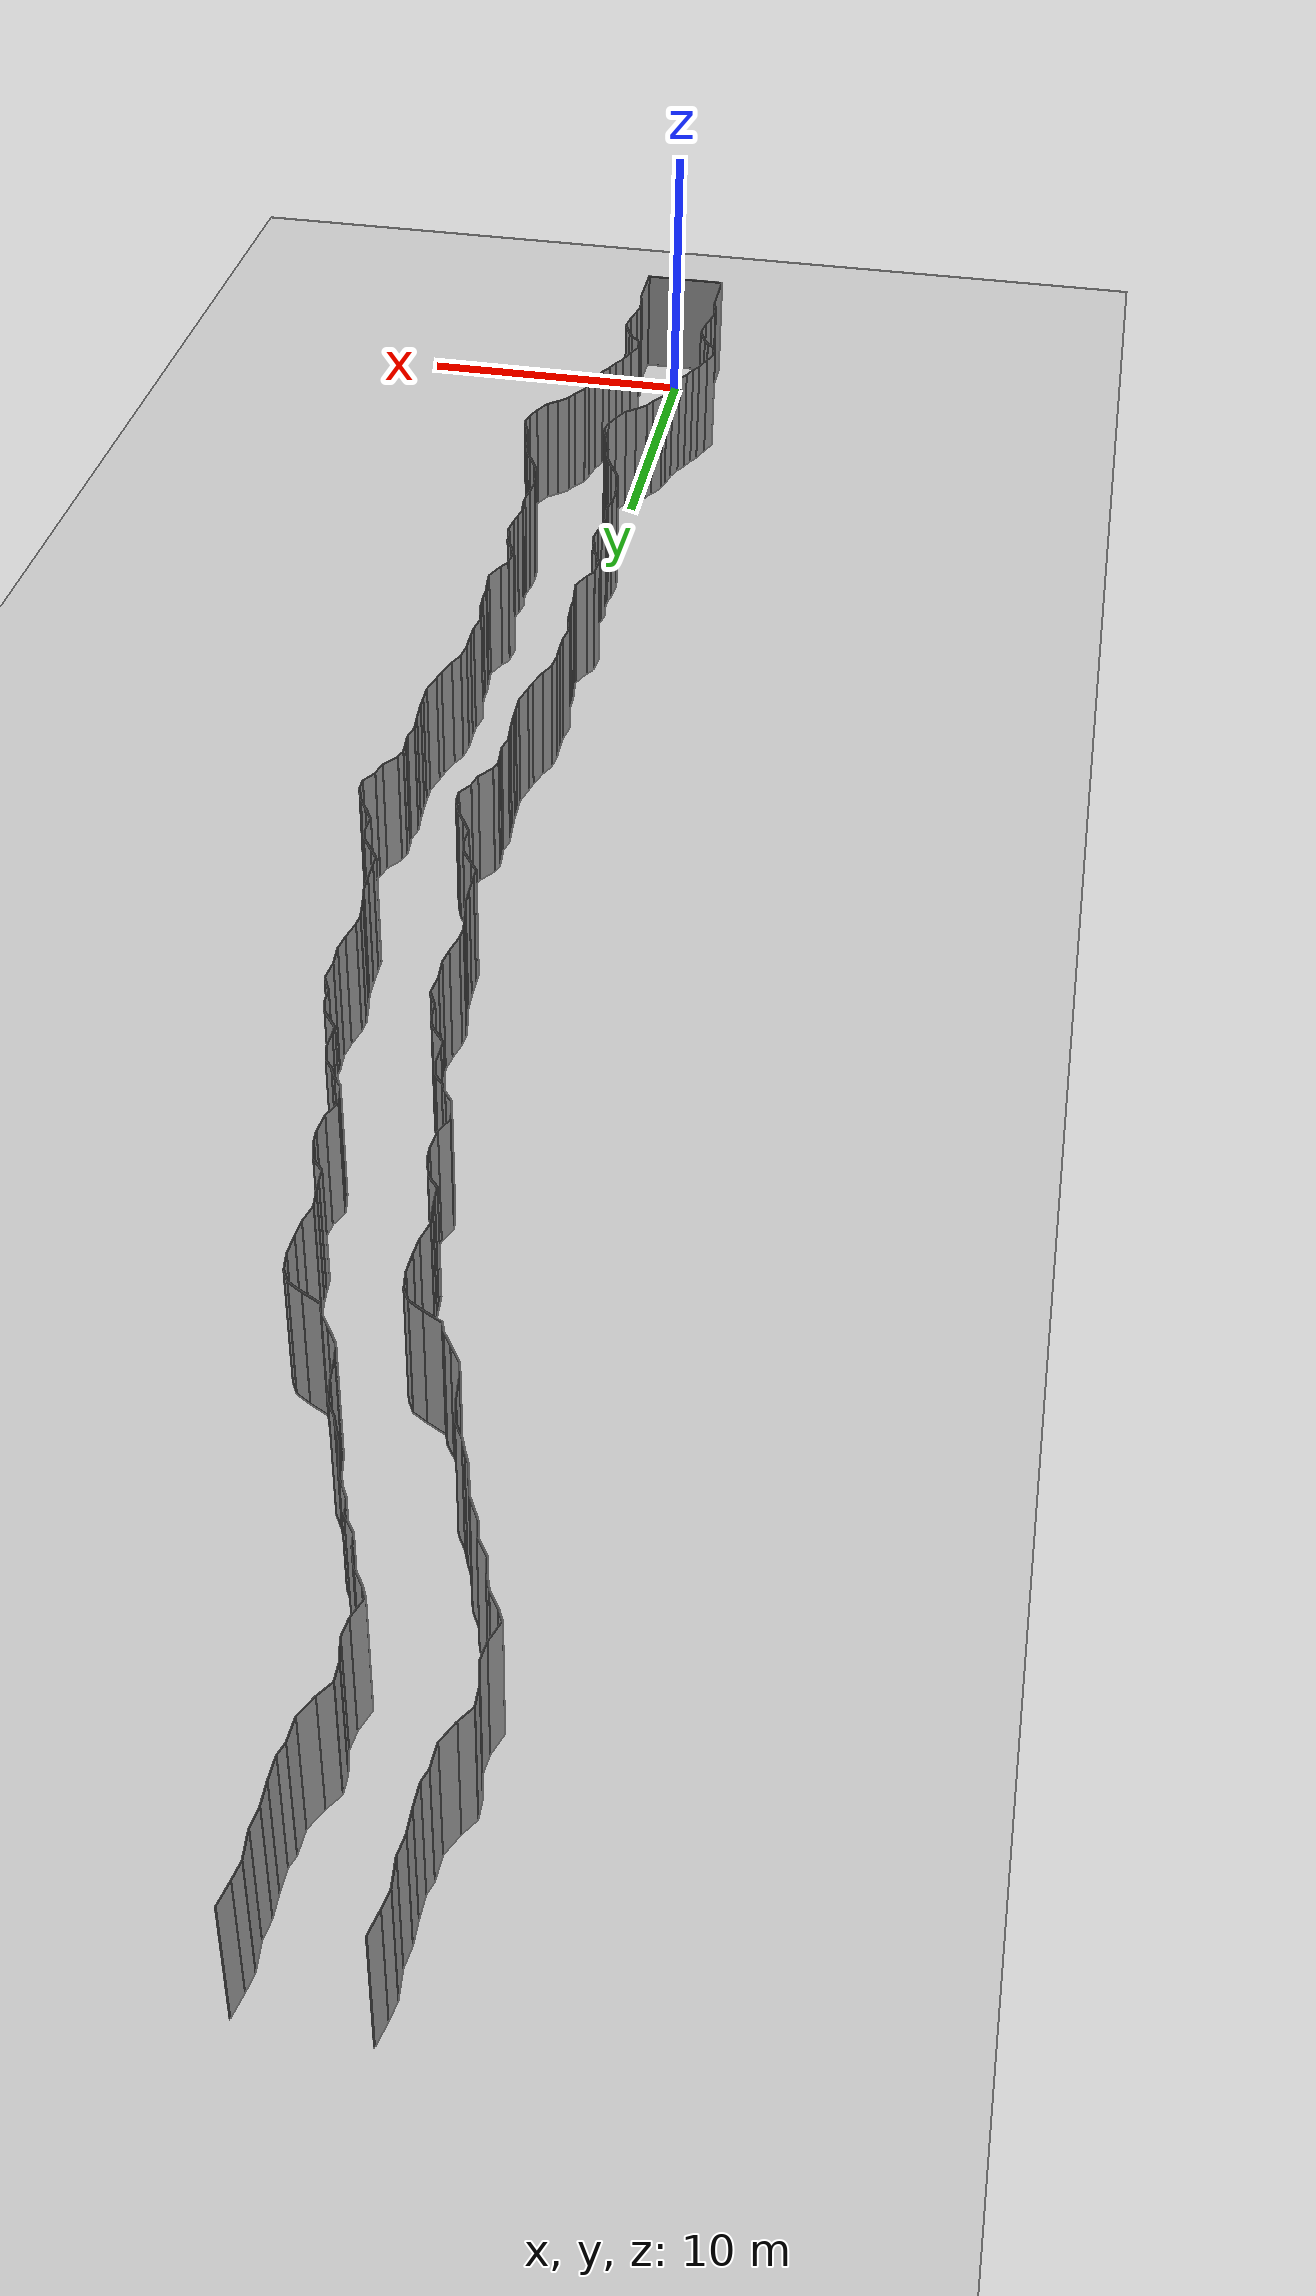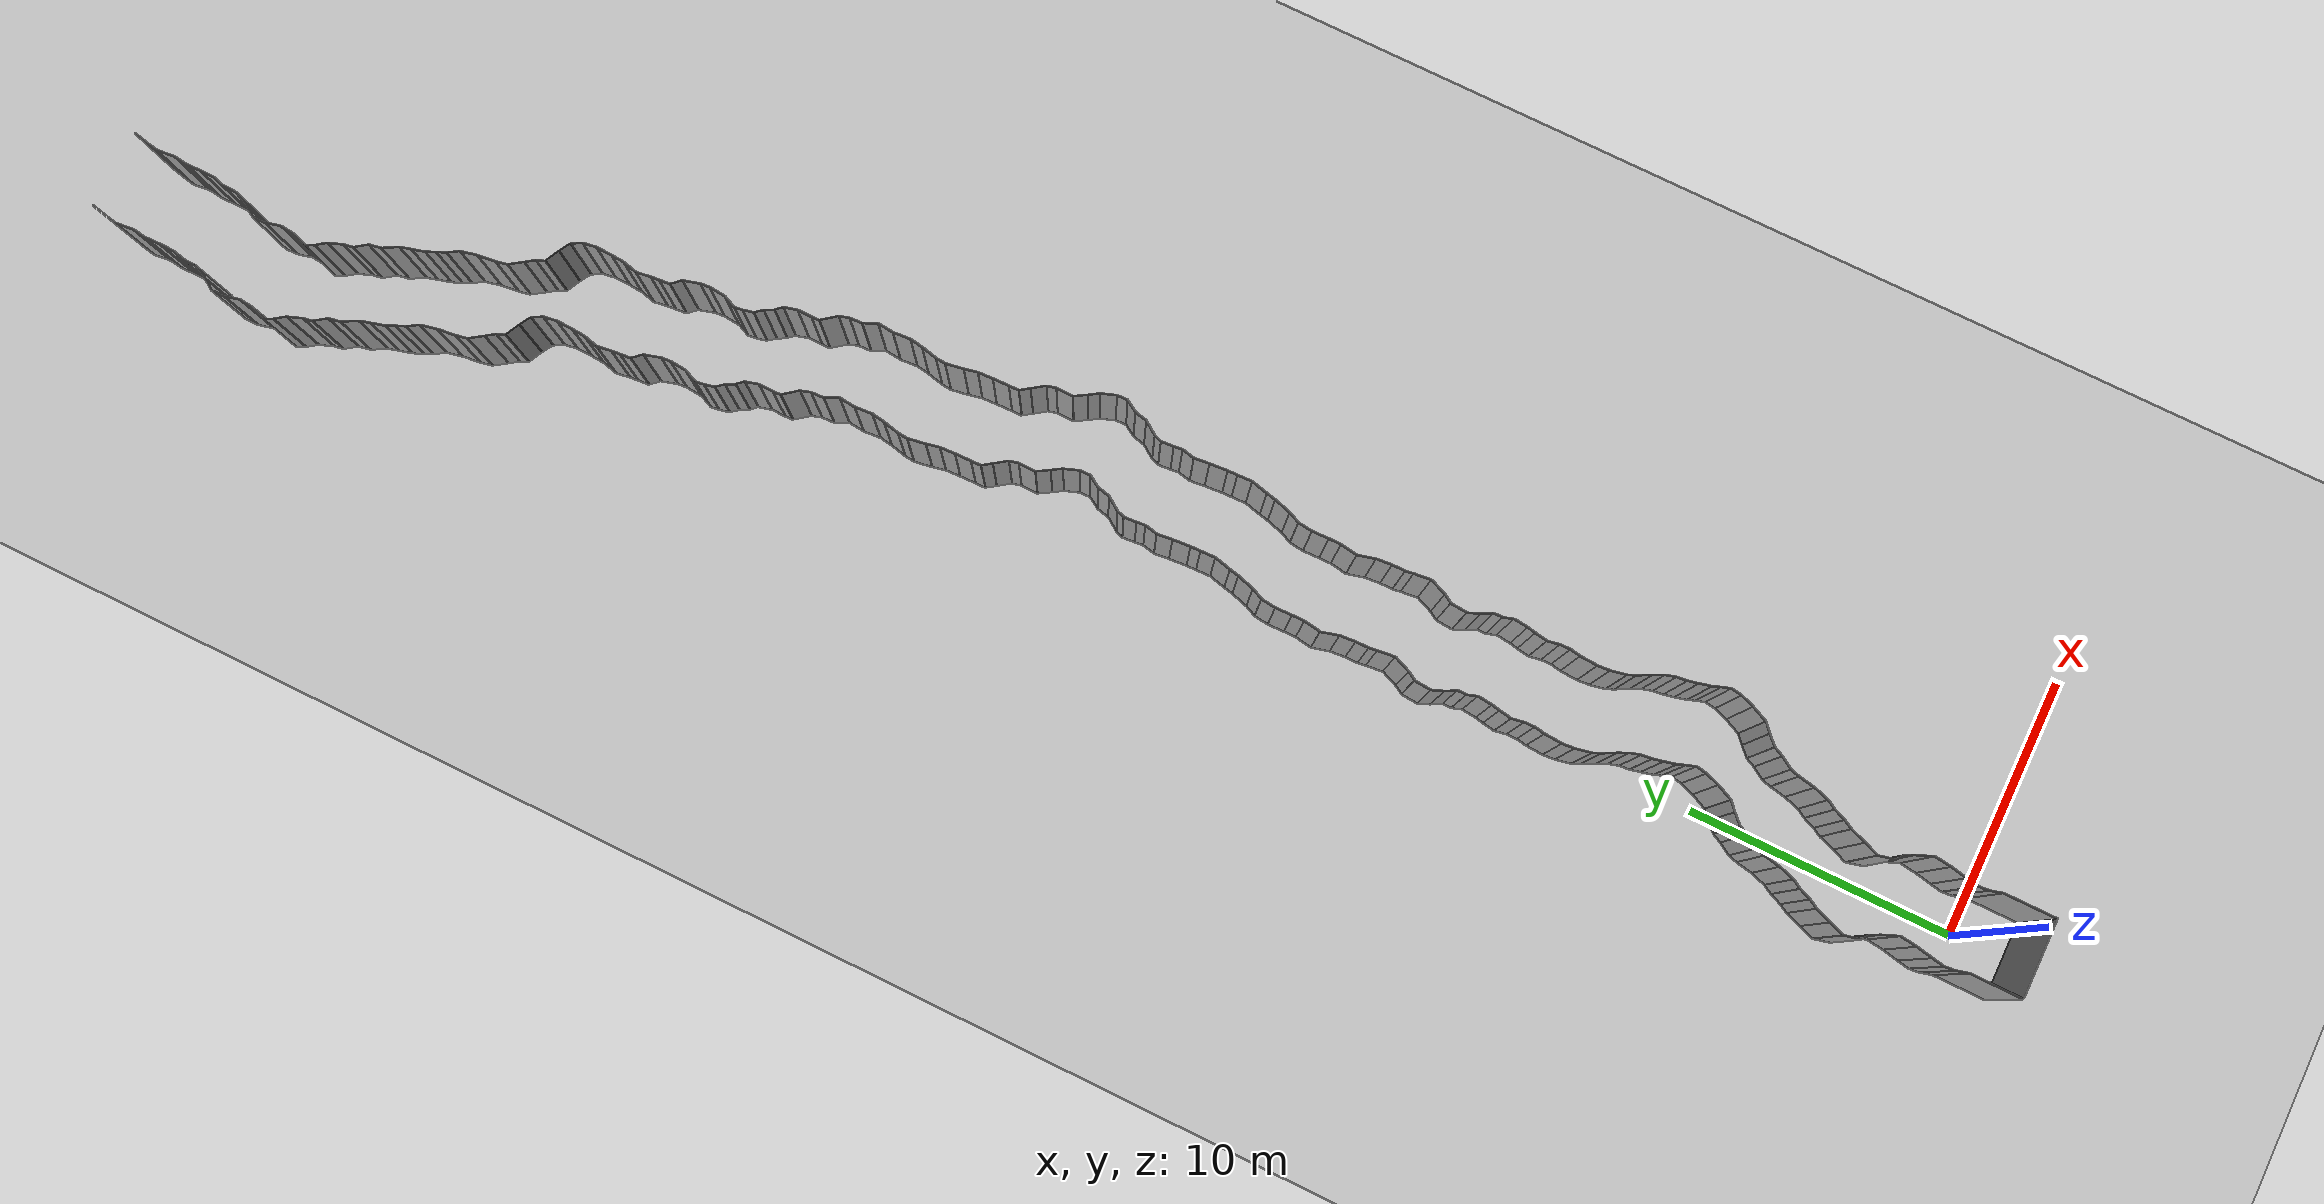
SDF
<sdf version="1.6">
 <world name="default">
  <light name="sun" type="directional">
   <pose>0 0 10 0 -0 0</pose>
   <diffuse>0.8 0.8 0.8 1</diffuse>
   <specular>0.2 0.2 0.2 1</specular>
   <attenuation>
    <range>1000</range>
    <constant>0.9</constant>
    <linear>0.01</linear>
    <quadratic>0.001</quadratic>
   </attenuation>
   <direction>-0.5 0.1 -0.9</direction>
  </light>
  <model name="ground_plane">
   <static>1</static>
   <link name="link">
    <collision name="collision">
     <geometry><plane><normal>0 0 1</normal><size>200 200</size></plane></geometry>
     <surface><friction><ode><mu>100</mu><mu2>50</mu2></ode></friction></surface>
    </collision>
    <visual name="visual">
     <cast_shadows>0</cast_shadows>
     <geometry><plane><normal>0 0 1</normal><size>200 200</size></plane></geometry>
     <material>
      <script><uri>file://media/materials/scripts/gazebo.material</uri><name>Gazebo/Grey</name></script>
     </material>
    </visual>
   </link>
   <pose>0 100 0 0 -0 0</pose>
  </model>
  <gravity>0 0 -9.8</gravity>
  <magnetic_field>6e-06 2.3e-05 -4.2e-05</magnetic_field>
  <atmosphere type="adiabatic"/>
  <physics default="0" name="default_physics" type="ode">
   <max_step_size>0.001</max_step_size>
   <real_time_factor>1</real_time_factor>
   <real_time_update_rate>1000</real_time_update_rate>
  </physics>
  <scene><ambient>0.4 0.4 0.4 1</ambient><background>0.7 0.7 0.7 1</background><shadows>1</shadows></scene>
  <spherical_coordinates>
   <surface_model>EARTH_WGS84</surface_model>
   <latitude_deg>0</latitude_deg>
   <longitude_deg>0</longitude_deg>
   <elevation>0</elevation>
   <heading_deg>0</heading_deg>
  </spherical_coordinates>
  <model name="wall_back">
   <static>1</static>
   <pose>0.0 -2 2 0.0 0 0.0</pose>
   <link name="link">
    <collision name="collision"><geometry><box><size>3 0.02 4</size></box></geometry></collision>
    <visual name="visual">
     <material>
      <script><name>Gazebo/Grey</name><uri>file://media/materials/scripts/gazebo.material</uri></script>
     </material>
     <geometry><box><size>3 0.02 4</size></box></geometry>
    </visual>
   </link>
  </model>
  <model name="wall_left">
   <static>1</static>
   <pose>1.5 -1 2 0 0 0.00</pose>
   <link name="link">
    <collision name="collision"><geometry><box><size>0.02 2 4</size></box></geometry></collision>
    <visual name="visual">
     <material>
      <script><name>Gazebo/Grey</name><uri>file://media/materials/scripts/gazebo.material</uri></script>
     </material>
     <geometry><box><size>0.02 2 4</size></box></geometry>
    </visual>
   </link>
  </model>
  <model name="wall_right">
   <static>1</static>
   <pose>-1.5 -1 2 0 0 0.00</pose>
   <link name="link">
    <collision name="collision"><geometry><box><size>0.02 2 4</size></box></geometry></collision>
    <visual name="visual">
     <material>
      <script><name>Gazebo/Grey</name><uri>file://media/materials/scripts/gazebo.material</uri></script>
     </material>
     <geometry><box><size>0.02 2 4</size></box></geometry>
    </visual>
   </link>
  </model>
  <model name="wall_0">
   <static>1</static>
   <pose>-1.565739611500595 0.24088608216315852 2 0 0 0.2664197645561969</pose>
   <link name="link">
    <collision name="collision"><geometry><box><size>0.02 0.499390833317 4</size></box></geometry></collision>
    <visual name="visual">
     <material>
      <script><name>Gazebo/Grey</name><uri>file://media/materials/scripts/gazebo.material</uri></script>
     </material>
     <geometry><box><size>0.02 0.499390833317 4</size></box></geometry>
    </visual>
   </link>
  </model>
  <model name="wall_1">
   <static>1</static>
   <pose>1.434260388499405 0.24088608216315852 2 0 0 0.2664197645561969</pose>
   <link name="link">
    <collision name="collision"><geometry><box><size>0.02 0.499390833317 4</size></box></geometry></collision>
    <visual name="visual">
     <material>
      <script><name>Gazebo/Grey</name><uri>file://media/materials/scripts/gazebo.material</uri></script>
     </material>
     <geometry><box><size>0.02 0.499390833317 4</size></box></geometry>
    </visual>
   </link>
  </model>
  <model name="wall_2">
   <static>1</static>
   <pose>-1.6483853456226922 0.6741960241709141 2 0 0 0.08763374060429269</pose>
   <link name="link">
    <collision name="collision"><geometry><box><size>0.02 0.386330215332 4</size></box></geometry></collision>
    <visual name="visual">
     <material>
      <script><name>Gazebo/Grey</name><uri>file://media/materials/scripts/gazebo.material</uri></script>
     </material>
     <geometry><box><size>0.02 0.386330215332 4</size></box></geometry>
    </visual>
   </link>
  </model>
  <model name="wall_3">
   <static>1</static>
   <pose>1.3516146543773078 0.6741960241709141 2 0 0 0.08763374060429269</pose>
   <link name="link">
    <collision name="collision"><geometry><box><size>0.02 0.386330215332 4</size></box></geometry></collision>
    <visual name="visual">
     <material>
      <script><name>Gazebo/Grey</name><uri>file://media/materials/scripts/gazebo.material</uri></script>
     </material>
     <geometry><box><size>0.02 0.386330215332 4</size></box></geometry>
    </visual>
   </link>
  </model>
  <model name="wall_4">
   <static>1</static>
   <pose>-1.6224939898118325 1.0997063646286278 2 0 0 -0.18158938076499426</pose>
   <link name="link">
    <collision name="collision"><geometry><box><size>0.02 0.473965954916 4</size></box></geometry></collision>
    <visual name="visual">
     <material>
      <script><name>Gazebo/Grey</name><uri>file://media/materials/scripts/gazebo.material</uri></script>
     </material>
     <geometry><box><size>0.02 0.473965954916 4</size></box></geometry>
    </visual>
   </link>
  </model>
  <model name="wall_5">
   <static>1</static>
   <pose>1.3775060101881675 1.0997063646286278 2 0 0 -0.18158938076499426</pose>
   <link name="link">
    <collision name="collision"><geometry><box><size>0.02 0.473965954916 4</size></box></geometry></collision>
    <visual name="visual">
     <material>
      <script><name>Gazebo/Grey</name><uri>file://media/materials/scripts/gazebo.material</uri></script>
     </material>
     <geometry><box><size>0.02 0.473965954916 4</size></box></geometry>
    </visual>
   </link>
  </model>
  <model name="wall_6">
   <static>1</static>
   <pose>-1.5172936481979964 1.6427296880698645 2 0 0 -0.1986842445359933</pose>
   <link name="link">
    <collision name="collision"><geometry><box><size>0.02 0.632313099265 4</size></box></geometry></collision>
    <visual name="visual">
     <material>
      <script><name>Gazebo/Grey</name><uri>file://media/materials/scripts/gazebo.material</uri></script>
     </material>
     <geometry><box><size>0.02 0.632313099265 4</size></box></geometry>
    </visual>
   </link>
  </model>
  <model name="wall_7">
   <static>1</static>
   <pose>1.4827063518020036 1.6427296880698645 2 0 0 -0.1986842445359933</pose>
   <link name="link">
    <collision name="collision"><geometry><box><size>0.02 0.632313099265 4</size></box></geometry></collision>
    <visual name="visual">
     <material>
      <script><name>Gazebo/Grey</name><uri>file://media/materials/scripts/gazebo.material</uri></script>
     </material>
     <geometry><box><size>0.02 0.632313099265 4</size></box></geometry>
    </visual>
   </link>
  </model>
  <model name="wall_8">
   <static>1</static>
   <pose>-1.4136420460431394 2.273343459773019 2 0 0 -0.12792773836013294</pose>
   <link name="link">
    <collision name="collision"><geometry><box><size>0.02 0.646637923972 4</size></box></geometry></collision>
    <visual name="visual">
     <material>
      <script><name>Gazebo/Grey</name><uri>file://media/materials/scripts/gazebo.material</uri></script>
     </material>
     <geometry><box><size>0.02 0.646637923972 4</size></box></geometry>
    </visual>
   </link>
  </model>
  <model name="wall_9">
   <static>1</static>
   <pose>1.5863579539568606 2.273343459773019 2 0 0 -0.12792773836013294</pose>
   <link name="link">
    <collision name="collision"><geometry><box><size>0.02 0.646637923972 4</size></box></geometry></collision>
    <visual name="visual">
     <material>
      <script><name>Gazebo/Grey</name><uri>file://media/materials/scripts/gazebo.material</uri></script>
     </material>
     <geometry><box><size>0.02 0.646637923972 4</size></box></geometry>
    </visual>
   </link>
  </model>
  <model name="wall_10">
   <static>1</static>
   <pose>-1.5021101102420251 2.9108111238589625 2 0 0 0.38864477231435324</pose>
   <link name="link">
    <collision name="collision"><geometry><box><size>0.02 0.684639522495 4</size></box></geometry></collision>
    <visual name="visual">
     <material>
      <script><name>Gazebo/Grey</name><uri>file://media/materials/scripts/gazebo.material</uri></script>
     </material>
     <geometry><box><size>0.02 0.684639522495 4</size></box></geometry>
    </visual>
   </link>
  </model>
  <model name="wall_11">
   <static>1</static>
   <pose>1.4978898897579749 2.9108111238589625 2 0 0 0.38864477231435324</pose>
   <link name="link">
    <collision name="collision"><geometry><box><size>0.02 0.684639522495 4</size></box></geometry></collision>
    <visual name="visual">
     <material>
      <script><name>Gazebo/Grey</name><uri>file://media/materials/scripts/gazebo.material</uri></script>
     </material>
     <geometry><box><size>0.02 0.684639522495 4</size></box></geometry>
    </visual>
   </link>
  </model>
  <model name="wall_12">
   <static>1</static>
   <pose>-1.7144954054000514 3.380717711754754 2 0 0 0.4950621232531164</pose>
   <link name="link">
    <collision name="collision"><geometry><box><size>0.02 0.348014619869 4</size></box></geometry></collision>
    <visual name="visual">
     <material>
      <script><name>Gazebo/Grey</name><uri>file://media/materials/scripts/gazebo.material</uri></script>
     </material>
     <geometry><box><size>0.02 0.348014619869 4</size></box></geometry>
    </visual>
   </link>
  </model>
  <model name="wall_13">
   <static>1</static>
   <pose>1.2855045945999486 3.380717711754754 2 0 0 0.4950621232531164</pose>
   <link name="link">
    <collision name="collision"><geometry><box><size>0.02 0.348014619869 4</size></box></geometry></collision>
    <visual name="visual">
     <material>
      <script><name>Gazebo/Grey</name><uri>file://media/materials/scripts/gazebo.material</uri></script>
     </material>
     <geometry><box><size>0.02 0.348014619869 4</size></box></geometry>
    </visual>
   </link>
  </model>
  <model name="wall_14">
   <static>1</static>
   <pose>-1.9208575377017132 3.6237284901054827 2 0 0 0.9423389882361022</pose>
   <link name="link">
    <collision name="collision"><geometry><box><size>0.02 0.305818340294 4</size></box></geometry></collision>
    <visual name="visual">
     <material>
      <script><name>Gazebo/Grey</name><uri>file://media/materials/scripts/gazebo.material</uri></script>
     </material>
     <geometry><box><size>0.02 0.305818340294 4</size></box></geometry>
    </visual>
   </link>
  </model>
  <model name="wall_15">
   <static>1</static>
   <pose>1.0791424622982868 3.6237284901054827 2 0 0 0.9423389882361022</pose>
   <link name="link">
    <collision name="collision"><geometry><box><size>0.02 0.305818340294 4</size></box></geometry></collision>
    <visual name="visual">
     <material>
      <script><name>Gazebo/Grey</name><uri>file://media/materials/scripts/gazebo.material</uri></script>
     </material>
     <geometry><box><size>0.02 0.305818340294 4</size></box></geometry>
    </visual>
   </link>
  </model>
  <model name="wall_16">
   <static>1</static>
   <pose>-2.121650649095559 4.036127716997495 2 0 0 0.2346606584070033</pose>
   <link name="link">
    <collision name="collision"><geometry><box><size>0.02 0.663184296406 4</size></box></geometry></collision>
    <visual name="visual">
     <material>
      <script><name>Gazebo/Grey</name><uri>file://media/materials/scripts/gazebo.material</uri></script>
     </material>
     <geometry><box><size>0.02 0.663184296406 4</size></box></geometry>
    </visual>
   </link>
  </model>
  <model name="wall_17">
   <static>1</static>
   <pose>0.8783493509044411 4.036127716997495 2 0 0 0.2346606584070033</pose>
   <link name="link">
    <collision name="collision"><geometry><box><size>0.02 0.663184296406 4</size></box></geometry></collision>
    <visual name="visual">
     <material>
      <script><name>Gazebo/Grey</name><uri>file://media/materials/scripts/gazebo.material</uri></script>
     </material>
     <geometry><box><size>0.02 0.663184296406 4</size></box></geometry>
    </visual>
   </link>
  </model>
  <model name="wall_18">
   <static>1</static>
   <pose>-2.091013936563034 4.639162786583809 2 0 0 -0.36667606427582305</pose>
   <link name="link">
    <collision name="collision"><geometry><box><size>0.02 0.601014466567 4</size></box></geometry></collision>
    <visual name="visual">
     <material>
      <script><name>Gazebo/Grey</name><uri>file://media/materials/scripts/gazebo.material</uri></script>
     </material>
     <geometry><box><size>0.02 0.601014466567 4</size></box></geometry>
    </visual>
   </link>
  </model>
  <model name="wall_19">
   <static>1</static>
   <pose>0.908986063436966 4.639162786583809 2 0 0 -0.36667606427582305</pose>
   <link name="link">
    <collision name="collision"><geometry><box><size>0.02 0.601014466567 4</size></box></geometry></collision>
    <visual name="visual">
     <material>
      <script><name>Gazebo/Grey</name><uri>file://media/materials/scripts/gazebo.material</uri></script>
     </material>
     <geometry><box><size>0.02 0.601014466567 4</size></box></geometry>
    </visual>
   </link>
  </model>
  <model name="wall_20">
   <static>1</static>
   <pose>-1.8745241503220937 5.220819056604774 2 0 0 -0.3465795173068685</pose>
   <link name="link">
    <collision name="collision"><geometry><box><size>0.02 0.640324648395 4</size></box></geometry></collision>
    <visual name="visual">
     <material>
      <script><name>Gazebo/Grey</name><uri>file://media/materials/scripts/gazebo.material</uri></script>
     </material>
     <geometry><box><size>0.02 0.640324648395 4</size></box></geometry>
    </visual>
   </link>
  </model>
  <model name="wall_21">
   <static>1</static>
   <pose>1.1254758496779063 5.220819056604774 2 0 0 -0.3465795173068685</pose>
   <link name="link">
    <collision name="collision"><geometry><box><size>0.02 0.640324648395 4</size></box></geometry></collision>
    <visual name="visual">
     <material>
      <script><name>Gazebo/Grey</name><uri>file://media/materials/scripts/gazebo.material</uri></script>
     </material>
     <geometry><box><size>0.02 0.640324648395 4</size></box></geometry>
    </visual>
   </link>
  </model>
  <model name="wall_22">
   <static>1</static>
   <pose>-1.6711643647316854 5.685106192930393 2 0 0 -0.5254573671960013</pose>
   <link name="link">
    <collision name="collision"><geometry><box><size>0.02 0.377211075557 4</size></box></geometry></collision>
    <visual name="visual">
     <material>
      <script><name>Gazebo/Grey</name><uri>file://media/materials/scripts/gazebo.material</uri></script>
     </material>
     <geometry><box><size>0.02 0.377211075557 4</size></box></geometry>
    </visual>
   </link>
  </model>
  <model name="wall_23">
   <static>1</static>
   <pose>1.3288356352683146 5.685106192930393 2 0 0 -0.5254573671960013</pose>
   <link name="link">
    <collision name="collision"><geometry><box><size>0.02 0.377211075557 4</size></box></geometry></collision>
    <visual name="visual">
     <material>
      <script><name>Gazebo/Grey</name><uri>file://media/materials/scripts/gazebo.material</uri></script>
     </material>
     <geometry><box><size>0.02 0.377211075557 4</size></box></geometry>
    </visual>
   </link>
  </model>
  <model name="wall_24">
   <static>1</static>
   <pose>-1.4870901184349976 6.069999245519834 2 0 0 -0.3835177855792076</pose>
   <link name="link">
    <collision name="collision"><geometry><box><size>0.02 0.478202283776 4</size></box></geometry></collision>
    <visual name="visual">
     <material>
      <script><name>Gazebo/Grey</name><uri>file://media/materials/scripts/gazebo.material</uri></script>
     </material>
     <geometry><box><size>0.02 0.478202283776 4</size></box></geometry>
    </visual>
   </link>
  </model>
  <model name="wall_25">
   <static>1</static>
   <pose>1.5129098815650024 6.069999245519834 2 0 0 -0.3835177855792076</pose>
   <link name="link">
    <collision name="collision"><geometry><box><size>0.02 0.478202283776 4</size></box></geometry></collision>
    <visual name="visual">
     <material>
      <script><name>Gazebo/Grey</name><uri>file://media/materials/scripts/gazebo.material</uri></script>
     </material>
     <geometry><box><size>0.02 0.478202283776 4</size></box></geometry>
    </visual>
   </link>
  </model>
  <model name="wall_26">
   <static>1</static>
   <pose>-1.2980619678183172 6.460374131454251 2 0 0 -0.5332999212025807</pose>
   <link name="link">
    <collision name="collision"><geometry><box><size>0.02 0.391677572917 4</size></box></geometry></collision>
    <visual name="visual">
     <material>
      <script><name>Gazebo/Grey</name><uri>file://media/materials/scripts/gazebo.material</uri></script>
     </material>
     <geometry><box><size>0.02 0.391677572917 4</size></box></geometry>
    </visual>
   </link>
  </model>
  <model name="wall_27">
   <static>1</static>
   <pose>1.7019380321816828 6.460374131454251 2 0 0 -0.5332999212025807</pose>
   <link name="link">
    <collision name="collision"><geometry><box><size>0.02 0.391677572917 4</size></box></geometry></collision>
    <visual name="visual">
     <material>
      <script><name>Gazebo/Grey</name><uri>file://media/materials/scripts/gazebo.material</uri></script>
     </material>
     <geometry><box><size>0.02 0.391677572917 4</size></box></geometry>
    </visual>
   </link>
  </model>
  <model name="wall_28">
   <static>1</static>
   <pose>-1.104667693843315 6.921692049198197 2 0 0 -0.31025566221828826</pose>
   <link name="link">
    <collision name="collision"><geometry><box><size>0.02 0.614697285239 4</size></box></geometry></collision>
    <visual name="visual">
     <material>
      <script><name>Gazebo/Grey</name><uri>file://media/materials/scripts/gazebo.material</uri></script>
     </material>
     <geometry><box><size>0.02 0.614697285239 4</size></box></geometry>
    </visual>
   </link>
  </model>
  <model name="wall_29">
   <static>1</static>
   <pose>1.895332306156685 6.921692049198197 2 0 0 -0.31025566221828826</pose>
   <link name="link">
    <collision name="collision"><geometry><box><size>0.02 0.614697285239 4</size></box></geometry></collision>
    <visual name="visual">
     <material>
      <script><name>Gazebo/Grey</name><uri>file://media/materials/scripts/gazebo.material</uri></script>
     </material>
     <geometry><box><size>0.02 0.614697285239 4</size></box></geometry>
    </visual>
   </link>
  </model>
  <model name="wall_30">
   <static>1</static>
   <pose>-0.9524156585972603 7.527631878212156 2 0 0 -0.18436278185102173</pose>
   <link name="link">
    <collision name="collision"><geometry><box><size>0.02 0.637331445591 4</size></box></geometry></collision>
    <visual name="visual">
     <material>
      <script><name>Gazebo/Grey</name><uri>file://media/materials/scripts/gazebo.material</uri></script>
     </material>
     <geometry><box><size>0.02 0.637331445591 4</size></box></geometry>
    </visual>
   </link>
  </model>
  <model name="wall_31">
   <static>1</static>
   <pose>2.0475843414027395 7.527631878212156 2 0 0 -0.18436278185102173</pose>
   <link name="link">
    <collision name="collision"><geometry><box><size>0.02 0.637331445591 4</size></box></geometry></collision>
    <visual name="visual">
     <material>
      <script><name>Gazebo/Grey</name><uri>file://media/materials/scripts/gazebo.material</uri></script>
     </material>
     <geometry><box><size>0.02 0.637331445591 4</size></box></geometry>
    </visual>
   </link>
  </model>
  <model name="wall_32">
   <static>1</static>
   <pose>-0.8461826182124886 8.015372793796 2 0 0 -0.26748370132998434</pose>
   <link name="link">
    <collision name="collision"><geometry><box><size>0.02 0.361817663133 4</size></box></geometry></collision>
    <visual name="visual">
     <material>
      <script><name>Gazebo/Grey</name><uri>file://media/materials/scripts/gazebo.material</uri></script>
     </material>
     <geometry><box><size>0.02 0.361817663133 4</size></box></geometry>
    </visual>
   </link>
  </model>
  <model name="wall_33">
   <static>1</static>
   <pose>2.1538173817875115 8.015372793796 2 0 0 -0.26748370132998434</pose>
   <link name="link">
    <collision name="collision"><geometry><box><size>0.02 0.361817663133 4</size></box></geometry></collision>
    <visual name="visual">
     <material>
      <script><name>Gazebo/Grey</name><uri>file://media/materials/scripts/gazebo.material</uri></script>
     </material>
     <geometry><box><size>0.02 0.361817663133 4</size></box></geometry>
    </visual>
   </link>
  </model>
  <model name="wall_34">
   <static>1</static>
   <pose>-0.6531005107113629 8.414410567422077 2 0 0 -0.574185349997685</pose>
   <link name="link">
    <collision name="collision"><geometry><box><size>0.02 0.534904384796 4</size></box></geometry></collision>
    <visual name="visual">
     <material>
      <script><name>Gazebo/Grey</name><uri>file://media/materials/scripts/gazebo.material</uri></script>
     </material>
     <geometry><box><size>0.02 0.534904384796 4</size></box></geometry>
    </visual>
   </link>
  </model>
  <model name="wall_35">
   <static>1</static>
   <pose>2.3468994892886372 8.414410567422077 2 0 0 -0.574185349997685</pose>
   <link name="link">
    <collision name="collision"><geometry><box><size>0.02 0.534904384796 4</size></box></geometry></collision>
    <visual name="visual">
     <material>
      <script><name>Gazebo/Grey</name><uri>file://media/materials/scripts/gazebo.material</uri></script>
     </material>
     <geometry><box><size>0.02 0.534904384796 4</size></box></geometry>
    </visual>
   </link>
  </model>
  <model name="wall_36">
   <static>1</static>
   <pose>-0.4227081682132432 8.815440413093574 2 0 0 -0.44945702265359894</pose>
   <link name="link">
    <collision name="collision"><geometry><box><size>0.02 0.391852804454 4</size></box></geometry></collision>
    <visual name="visual">
     <material>
      <script><name>Gazebo/Grey</name><uri>file://media/materials/scripts/gazebo.material</uri></script>
     </material>
     <geometry><box><size>0.02 0.391852804454 4</size></box></geometry>
    </visual>
   </link>
  </model>
  <model name="wall_37">
   <static>1</static>
   <pose>2.5772918317867566 8.815440413093574 2 0 0 -0.44945702265359894</pose>
   <link name="link">
    <collision name="collision"><geometry><box><size>0.02 0.391852804454 4</size></box></geometry></collision>
    <visual name="visual">
     <material>
      <script><name>Gazebo/Grey</name><uri>file://media/materials/scripts/gazebo.material</uri></script>
     </material>
     <geometry><box><size>0.02 0.391852804454 4</size></box></geometry>
    </visual>
   </link>
  </model>
  <model name="wall_38">
   <static>1</static>
   <pose>-0.16149954600914299 9.164619360388333 2 0 0 -0.7950650333283734</pose>
   <link name="link">
    <collision name="collision"><geometry><box><size>0.02 0.49329300945 4</size></box></geometry></collision>
    <visual name="visual">
     <material>
      <script><name>Gazebo/Grey</name><uri>file://media/materials/scripts/gazebo.material</uri></script>
     </material>
     <geometry><box><size>0.02 0.49329300945 4</size></box></geometry>
    </visual>
   </link>
  </model>
  <model name="wall_39">
   <static>1</static>
   <pose>2.838500453990857 9.164619360388333 2 0 0 -0.7950650333283734</pose>
   <link name="link">
    <collision name="collision"><geometry><box><size>0.02 0.49329300945 4</size></box></geometry></collision>
    <visual name="visual">
     <material>
      <script><name>Gazebo/Grey</name><uri>file://media/materials/scripts/gazebo.material</uri></script>
     </material>
     <geometry><box><size>0.02 0.49329300945 4</size></box></geometry>
    </visual>
   </link>
  </model>
  <model name="wall_40">
   <static>1</static>
   <pose>0.180669150913259 9.481449800055413 2 0 0 -0.8560927773171492</pose>
   <link name="link">
    <collision name="collision"><geometry><box><size>0.02 0.439794083715 4</size></box></geometry></collision>
    <visual name="visual">
     <material>
      <script><name>Gazebo/Grey</name><uri>file://media/materials/scripts/gazebo.material</uri></script>
     </material>
     <geometry><box><size>0.02 0.439794083715 4</size></box></geometry>
    </visual>
   </link>
  </model>
  <model name="wall_41">
   <static>1</static>
   <pose>3.180669150913259 9.481449800055413 2 0 0 -0.8560927773171492</pose>
   <link name="link">
    <collision name="collision"><geometry><box><size>0.02 0.439794083715 4</size></box></geometry></collision>
    <visual name="visual">
     <material>
      <script><name>Gazebo/Grey</name><uri>file://media/materials/scripts/gazebo.material</uri></script>
     </material>
     <geometry><box><size>0.02 0.439794083715 4</size></box></geometry>
    </visual>
   </link>
  </model>
  <model name="wall_42">
   <static>1</static>
   <pose>0.48522603566532 9.92372573289427 2 0 0 -0.4347845088825791</pose>
   <link name="link">
    <collision name="collision"><geometry><box><size>0.02 0.65748557552 4</size></box></geometry></collision>
    <visual name="visual">
     <material>
      <script><name>Gazebo/Grey</name><uri>file://media/materials/scripts/gazebo.material</uri></script>
     </material>
     <geometry><box><size>0.02 0.65748557552 4</size></box></geometry>
    </visual>
   </link>
  </model>
  <model name="wall_43">
   <static>1</static>
   <pose>3.48522603566532 9.92372573289427 2 0 0 -0.4347845088825791</pose>
   <link name="link">
    <collision name="collision"><geometry><box><size>0.02 0.65748557552 4</size></box></geometry></collision>
    <visual name="visual">
     <material>
      <script><name>Gazebo/Grey</name><uri>file://media/materials/scripts/gazebo.material</uri></script>
     </material>
     <geometry><box><size>0.02 0.65748557552 4</size></box></geometry>
    </visual>
   </link>
  </model>
  <model name="wall_44">
   <static>1</static>
   <pose>0.718601578090264 10.481962678245711 2 0 0 -0.34988975049354076</pose>
   <link name="link">
    <collision name="collision"><geometry><box><size>0.02 0.55370918265 4</size></box></geometry></collision>
    <visual name="visual">
     <material>
      <script><name>Gazebo/Grey</name><uri>file://media/materials/scripts/gazebo.material</uri></script>
     </material>
     <geometry><box><size>0.02 0.55370918265 4</size></box></geometry>
    </visual>
   </link>
  </model>
  <model name="wall_45">
   <static>1</static>
   <pose>3.718601578090264 10.481962678245711 2 0 0 -0.34988975049354076</pose>
   <link name="link">
    <collision name="collision"><geometry><box><size>0.02 0.55370918265 4</size></box></geometry></collision>
    <visual name="visual">
     <material>
      <script><name>Gazebo/Grey</name><uri>file://media/materials/scripts/gazebo.material</uri></script>
     </material>
     <geometry><box><size>0.02 0.55370918265 4</size></box></geometry>
    </visual>
   </link>
  </model>
  <model name="wall_46">
   <static>1</static>
   <pose>0.8462657989627398 10.945505000200539 2 0 0 -0.15964282527761284</pose>
   <link name="link">
    <collision name="collision"><geometry><box><size>0.02 0.412165462002 4</size></box></geometry></collision>
    <visual name="visual">
     <material>
      <script><name>Gazebo/Grey</name><uri>file://media/materials/scripts/gazebo.material</uri></script>
     </material>
     <geometry><box><size>0.02 0.412165462002 4</size></box></geometry>
    </visual>
   </link>
  </model>
  <model name="wall_47">
   <static>1</static>
   <pose>3.84626579896274 10.945505000200539 2 0 0 -0.15964282527761284</pose>
   <link name="link">
    <collision name="collision"><geometry><box><size>0.02 0.412165462002 4</size></box></geometry></collision>
    <visual name="visual">
     <material>
      <script><name>Gazebo/Grey</name><uri>file://media/materials/scripts/gazebo.material</uri></script>
     </material>
     <geometry><box><size>0.02 0.412165462002 4</size></box></geometry>
    </visual>
   </link>
  </model>
  <model name="wall_48">
   <static>1</static>
   <pose>0.8268747342737711 11.315957409230812 2 0 0 0.3027031251017241</pose>
   <link name="link">
    <collision name="collision"><geometry><box><size>0.02 0.349888364928 4</size></box></geometry></collision>
    <visual name="visual">
     <material>
      <script><name>Gazebo/Grey</name><uri>file://media/materials/scripts/gazebo.material</uri></script>
     </material>
     <geometry><box><size>0.02 0.349888364928 4</size></box></geometry>
    </visual>
   </link>
  </model>
  <model name="wall_49">
   <static>1</static>
   <pose>3.8268747342737712 11.315957409230812 2 0 0 0.3027031251017241</pose>
   <link name="link">
    <collision name="collision"><geometry><box><size>0.02 0.349888364928 4</size></box></geometry></collision>
    <visual name="visual">
     <material>
      <script><name>Gazebo/Grey</name><uri>file://media/materials/scripts/gazebo.material</uri></script>
     </material>
     <geometry><box><size>0.02 0.349888364928 4</size></box></geometry>
    </visual>
   </link>
  </model>
  <model name="wall_50">
   <static>1</static>
   <pose>0.719432858765186 11.626625338531646 2 0 0 0.3673562246984743</pose>
   <link name="link">
    <collision name="collision"><geometry><box><size>0.02 0.307898403709 4</size></box></geometry></collision>
    <visual name="visual">
     <material>
      <script><name>Gazebo/Grey</name><uri>file://media/materials/scripts/gazebo.material</uri></script>
     </material>
     <geometry><box><size>0.02 0.307898403709 4</size></box></geometry>
    </visual>
   </link>
  </model>
  <model name="wall_51">
   <static>1</static>
   <pose>3.719432858765186 11.626625338531646 2 0 0 0.3673562246984743</pose>
   <link name="link">
    <collision name="collision"><geometry><box><size>0.02 0.307898403709 4</size></box></geometry></collision>
    <visual name="visual">
     <material>
      <script><name>Gazebo/Grey</name><uri>file://media/materials/scripts/gazebo.material</uri></script>
     </material>
     <geometry><box><size>0.02 0.307898403709 4</size></box></geometry>
    </visual>
   </link>
  </model>
  <model name="wall_52">
   <static>1</static>
   <pose>0.6073412550380806 11.997077843059605 2 0 0 0.2454233593464097</pose>
   <link name="link">
    <collision name="collision"><geometry><box><size>0.02 0.467560203175 4</size></box></geometry></collision>
    <visual name="visual">
     <material>
      <script><name>Gazebo/Grey</name><uri>file://media/materials/scripts/gazebo.material</uri></script>
     </material>
     <geometry><box><size>0.02 0.467560203175 4</size></box></geometry>
    </visual>
   </link>
  </model>
  <model name="wall_53">
   <static>1</static>
   <pose>3.6073412550380803 11.997077843059605 2 0 0 0.2454233593464097</pose>
   <link name="link">
    <collision name="collision"><geometry><box><size>0.02 0.467560203175 4</size></box></geometry></collision>
    <visual name="visual">
     <material>
      <script><name>Gazebo/Grey</name><uri>file://media/materials/scripts/gazebo.material</uri></script>
     </material>
     <geometry><box><size>0.02 0.467560203175 4</size></box></geometry>
    </visual>
   </link>
  </model>
  <model name="wall_54">
   <static>1</static>
   <pose>0.5068886698628923 12.420343863029036 2 0 0 0.21860594444248038</pose>
   <link name="link">
    <collision name="collision"><geometry><box><size>0.02 0.402563201123 4</size></box></geometry></collision>
    <visual name="visual">
     <material>
      <script><name>Gazebo/Grey</name><uri>file://media/materials/scripts/gazebo.material</uri></script>
     </material>
     <geometry><box><size>0.02 0.402563201123 4</size></box></geometry>
    </visual>
   </link>
  </model>
  <model name="wall_55">
   <static>1</static>
   <pose>3.5068886698628923 12.420343863029036 2 0 0 0.21860594444248038</pose>
   <link name="link">
    <collision name="collision"><geometry><box><size>0.02 0.402563201123 4</size></box></geometry></collision>
    <visual name="visual">
     <material>
      <script><name>Gazebo/Grey</name><uri>file://media/materials/scripts/gazebo.material</uri></script>
     </material>
     <geometry><box><size>0.02 0.402563201123 4</size></box></geometry>
    </visual>
   </link>
  </model>
  <model name="wall_56">
   <static>1</static>
   <pose>0.4407977481680575 12.813623418107898 2 0 0 0.11353667303652037</pose>
   <link name="link">
    <collision name="collision"><geometry><box><size>0.02 0.396127032671 4</size></box></geometry></collision>
    <visual name="visual">
     <material>
      <script><name>Gazebo/Grey</name><uri>file://media/materials/scripts/gazebo.material</uri></script>
     </material>
     <geometry><box><size>0.02 0.396127032671 4</size></box></geometry>
    </visual>
   </link>
  </model>
  <model name="wall_57">
   <static>1</static>
   <pose>3.4407977481680576 12.813623418107898 2 0 0 0.11353667303652037</pose>
   <link name="link">
    <collision name="collision"><geometry><box><size>0.02 0.396127032671 4</size></box></geometry></collision>
    <visual name="visual">
     <material>
      <script><name>Gazebo/Grey</name><uri>file://media/materials/scripts/gazebo.material</uri></script>
     </material>
     <geometry><box><size>0.02 0.396127032671 4</size></box></geometry>
    </visual>
   </link>
  </model>
  <model name="wall_58">
   <static>1</static>
   <pose>0.36515695193584824 13.204656878645666 2 0 0 0.267333007421403</pose>
   <link name="link">
    <collision name="collision"><geometry><box><size>0.02 0.402798158126 4</size></box></geometry></collision>
    <visual name="visual">
     <material>
      <script><name>Gazebo/Grey</name><uri>file://media/materials/scripts/gazebo.material</uri></script>
     </material>
     <geometry><box><size>0.02 0.402798158126 4</size></box></geometry>
    </visual>
   </link>
  </model>
  <model name="wall_59">
   <static>1</static>
   <pose>3.365156951935848 13.204656878645666 2 0 0 0.267333007421403</pose>
   <link name="link">
    <collision name="collision"><geometry><box><size>0.02 0.402798158126 4</size></box></geometry></collision>
    <visual name="visual">
     <material>
      <script><name>Gazebo/Grey</name><uri>file://media/materials/scripts/gazebo.material</uri></script>
     </material>
     <geometry><box><size>0.02 0.402798158126 4</size></box></geometry>
    </visual>
   </link>
  </model>
  <model name="wall_60">
   <static>1</static>
   <pose>0.21986742679600613 13.59129624452851 2 0 0 0.4464155476808237</pose>
   <link name="link">
    <collision name="collision"><geometry><box><size>0.02 0.426594511705 4</size></box></geometry></collision>
    <visual name="visual">
     <material>
      <script><name>Gazebo/Grey</name><uri>file://media/materials/scripts/gazebo.material</uri></script>
     </material>
     <geometry><box><size>0.02 0.426594511705 4</size></box></geometry>
    </visual>
   </link>
  </model>
  <model name="wall_61">
   <static>1</static>
   <pose>3.2198674267960063 13.59129624452851 2 0 0 0.4464155476808237</pose>
   <link name="link">
    <collision name="collision"><geometry><box><size>0.02 0.426594511705 4</size></box></geometry></collision>
    <visual name="visual">
     <material>
      <script><name>Gazebo/Grey</name><uri>file://media/materials/scripts/gazebo.material</uri></script>
     </material>
     <geometry><box><size>0.02 0.426594511705 4</size></box></geometry>
    </visual>
   </link>
  </model>
  <model name="wall_62">
   <static>1</static>
   <pose>-0.003983334640508013 14.030411827023395 2 0 0 0.4905192048228044</pose>
   <link name="link">
    <collision name="collision"><geometry><box><size>0.02 0.559402821146 4</size></box></geometry></collision>
    <visual name="visual">
     <material>
      <script><name>Gazebo/Grey</name><uri>file://media/materials/scripts/gazebo.material</uri></script>
     </material>
     <geometry><box><size>0.02 0.559402821146 4</size></box></geometry>
    </visual>
   </link>
  </model>
  <model name="wall_63">
   <static>1</static>
   <pose>2.996016665359492 14.030411827023395 2 0 0 0.4905192048228044</pose>
   <link name="link">
    <collision name="collision"><geometry><box><size>0.02 0.559402821146 4</size></box></geometry></collision>
    <visual name="visual">
     <material>
      <script><name>Gazebo/Grey</name><uri>file://media/materials/scripts/gazebo.material</uri></script>
     </material>
     <geometry><box><size>0.02 0.559402821146 4</size></box></geometry>
    </visual>
   </link>
  </model>
  <model name="wall_64">
   <static>1</static>
   <pose>-0.19771399411953794 14.423380912522196 2 0 0 0.40078443767435995</pose>
   <link name="link">
    <collision name="collision"><geometry><box><size>0.02 0.31766904654 4</size></box></geometry></collision>
    <visual name="visual">
     <material>
      <script><name>Gazebo/Grey</name><uri>file://media/materials/scripts/gazebo.material</uri></script>
     </material>
     <geometry><box><size>0.02 0.31766904654 4</size></box></geometry>
    </visual>
   </link>
  </model>
  <model name="wall_65">
   <static>1</static>
   <pose>2.802286005880462 14.423380912522196 2 0 0 0.40078443767435995</pose>
   <link name="link">
    <collision name="collision"><geometry><box><size>0.02 0.31766904654 4</size></box></geometry></collision>
    <visual name="visual">
     <material>
      <script><name>Gazebo/Grey</name><uri>file://media/materials/scripts/gazebo.material</uri></script>
     </material>
     <geometry><box><size>0.02 0.31766904654 4</size></box></geometry>
    </visual>
   </link>
  </model>
  <model name="wall_66">
   <static>1</static>
   <pose>-0.31969712708149556 14.866710721906848 2 0 0 0.19933320098295287</pose>
   <link name="link">
    <collision name="collision"><geometry><box><size>0.02 0.606166995 4</size></box></geometry></collision>
    <visual name="visual">
     <material>
      <script><name>Gazebo/Grey</name><uri>file://media/materials/scripts/gazebo.material</uri></script>
     </material>
     <geometry><box><size>0.02 0.606166995 4</size></box></geometry>
    </visual>
   </link>
  </model>
  <model name="wall_67">
   <static>1</static>
   <pose>2.6803028729185043 14.866710721906848 2 0 0 0.19933320098295287</pose>
   <link name="link">
    <collision name="collision"><geometry><box><size>0.02 0.606166995 4</size></box></geometry></collision>
    <visual name="visual">
     <material>
      <script><name>Gazebo/Grey</name><uri>file://media/materials/scripts/gazebo.material</uri></script>
     </material>
     <geometry><box><size>0.02 0.606166995 4</size></box></geometry>
    </visual>
   </link>
  </model>
  <model name="wall_68">
   <static>1</static>
   <pose>-0.3987784305846526 15.395456126612928 2 0 0 0.08211535691355663</pose>
   <link name="link">
    <collision name="collision"><geometry><box><size>0.02 0.464893119417 4</size></box></geometry></collision>
    <visual name="visual">
     <material>
      <script><name>Gazebo/Grey</name><uri>file://media/materials/scripts/gazebo.material</uri></script>
     </material>
     <geometry><box><size>0.02 0.464893119417 4</size></box></geometry>
    </visual>
   </link>
  </model>
  <model name="wall_69">
   <static>1</static>
   <pose>2.6012215694153475 15.395456126612928 2 0 0 0.08211535691355663</pose>
   <link name="link">
    <collision name="collision"><geometry><box><size>0.02 0.464893119417 4</size></box></geometry></collision>
    <visual name="visual">
     <material>
      <script><name>Gazebo/Grey</name><uri>file://media/materials/scripts/gazebo.material</uri></script>
     </material>
     <geometry><box><size>0.02 0.464893119417 4</size></box></geometry>
    </visual>
   </link>
  </model>
  <model name="wall_70">
   <static>1</static>
   <pose>-0.39690742928138095 15.964101534812933 2 0 0 -0.062051105515447146</pose>
   <link name="link">
    <collision name="collision"><geometry><box><size>0.02 0.675263768146 4</size></box></geometry></collision>
    <visual name="visual">
     <material>
      <script><name>Gazebo/Grey</name><uri>file://media/materials/scripts/gazebo.material</uri></script>
     </material>
     <geometry><box><size>0.02 0.675263768146 4</size></box></geometry>
    </visual>
   </link>
  </model>
  <model name="wall_71">
   <static>1</static>
   <pose>2.603092570718619 15.964101534812933 2 0 0 -0.062051105515447146</pose>
   <link name="link">
    <collision name="collision"><geometry><box><size>0.02 0.675263768146 4</size></box></geometry></collision>
    <visual name="visual">
     <material>
      <script><name>Gazebo/Grey</name><uri>file://media/materials/scripts/gazebo.material</uri></script>
     </material>
     <geometry><box><size>0.02 0.675263768146 4</size></box></geometry>
    </visual>
   </link>
  </model>
  <model name="wall_72">
   <static>1</static>
   <pose>-0.3411308732283872 16.50026985802617 2 0 0 -0.1731578660085581</pose>
   <link name="link">
    <collision name="collision"><geometry><box><size>0.02 0.404420322567 4</size></box></geometry></collision>
    <visual name="visual">
     <material>
      <script><name>Gazebo/Grey</name><uri>file://media/materials/scripts/gazebo.material</uri></script>
     </material>
     <geometry><box><size>0.02 0.404420322567 4</size></box></geometry>
    </visual>
   </link>
  </model>
  <model name="wall_73">
   <static>1</static>
   <pose>2.658869126771613 16.50026985802617 2 0 0 -0.1731578660085581</pose>
   <link name="link">
    <collision name="collision"><geometry><box><size>0.02 0.404420322567 4</size></box></geometry></collision>
    <visual name="visual">
     <material>
      <script><name>Gazebo/Grey</name><uri>file://media/materials/scripts/gazebo.material</uri></script>
     </material>
     <geometry><box><size>0.02 0.404420322567 4</size></box></geometry>
    </visual>
   </link>
  </model>
  <model name="wall_74">
   <static>1</static>
   <pose>-0.3087108087761171 16.89664331656107 2 0 0 0.012269457442747742</pose>
   <link name="link">
    <collision name="collision"><geometry><box><size>0.02 0.394404144756 4</size></box></geometry></collision>
    <visual name="visual">
     <material>
      <script><name>Gazebo/Grey</name><uri>file://media/materials/scripts/gazebo.material</uri></script>
     </material>
     <geometry><box><size>0.02 0.394404144756 4</size></box></geometry>
    </visual>
   </link>
  </model>
  <model name="wall_75">
   <static>1</static>
   <pose>2.6912891912238828 16.89664331656107 2 0 0 0.012269457442747742</pose>
   <link name="link">
    <collision name="collision"><geometry><box><size>0.02 0.394404144756 4</size></box></geometry></collision>
    <visual name="visual">
     <material>
      <script><name>Gazebo/Grey</name><uri>file://media/materials/scripts/gazebo.material</uri></script>
     </material>
     <geometry><box><size>0.02 0.394404144756 4</size></box></geometry>
    </visual>
   </link>
  </model>
  <model name="wall_76">
   <static>1</static>
   <pose>-0.3530695926732368 17.322582289823302 2 0 0 0.18132595956905626</pose>
   <link name="link">
    <collision name="collision"><geometry><box><size>0.02 0.465129073691 4</size></box></geometry></collision>
    <visual name="visual">
     <material>
      <script><name>Gazebo/Grey</name><uri>file://media/materials/scripts/gazebo.material</uri></script>
     </material>
     <geometry><box><size>0.02 0.465129073691 4</size></box></geometry>
    </visual>
   </link>
  </model>
  <model name="wall_77">
   <static>1</static>
   <pose>2.646930407326763 17.322582289823302 2 0 0 0.18132595956905626</pose>
   <link name="link">
    <collision name="collision"><geometry><box><size>0.02 0.465129073691 4</size></box></geometry></collision>
    <visual name="visual">
     <material>
      <script><name>Gazebo/Grey</name><uri>file://media/materials/scripts/gazebo.material</uri></script>
     </material>
     <geometry><box><size>0.02 0.465129073691 4</size></box></geometry>
    </visual>
   </link>
  </model>
  <model name="wall_78">
   <static>1</static>
   <pose>-0.35659133693472317 17.789352559761916 2 0 0 -0.1600255368035915</pose>
   <link name="link">
    <collision name="collision"><geometry><box><size>0.02 0.482197992039 4</size></box></geometry></collision>
    <visual name="visual">
     <material>
      <script><name>Gazebo/Grey</name><uri>file://media/materials/scripts/gazebo.material</uri></script>
     </material>
     <geometry><box><size>0.02 0.482197992039 4</size></box></geometry>
    </visual>
   </link>
  </model>
  <model name="wall_79">
   <static>1</static>
   <pose>2.643408663065277 17.789352559761916 2 0 0 -0.1600255368035915</pose>
   <link name="link">
    <collision name="collision"><geometry><box><size>0.02 0.482197992039 4</size></box></geometry></collision>
    <visual name="visual">
     <material>
      <script><name>Gazebo/Grey</name><uri>file://media/materials/scripts/gazebo.material</uri></script>
     </material>
     <geometry><box><size>0.02 0.482197992039 4</size></box></geometry>
    </visual>
   </link>
  </model>
  <model name="wall_80">
   <static>1</static>
   <pose>-0.2866491413764098 18.18500765076612 2 0 0 -0.19737936277043475</pose>
   <link name="link">
    <collision name="collision"><geometry><box><size>0.02 0.321515727166 4</size></box></geometry></collision>
    <visual name="visual">
     <material>
      <script><name>Gazebo/Grey</name><uri>file://media/materials/scripts/gazebo.material</uri></script>
     </material>
     <geometry><box><size>0.02 0.321515727166 4</size></box></geometry>
    </visual>
   </link>
  </model>
  <model name="wall_81">
   <static>1</static>
   <pose>2.71335085862359 18.18500765076612 2 0 0 -0.19737936277043475</pose>
   <link name="link">
    <collision name="collision"><geometry><box><size>0.02 0.321515727166 4</size></box></geometry></collision>
    <visual name="visual">
     <material>
      <script><name>Gazebo/Grey</name><uri>file://media/materials/scripts/gazebo.material</uri></script>
     </material>
     <geometry><box><size>0.02 0.321515727166 4</size></box></geometry>
    </visual>
   </link>
  </model>
  <model name="wall_82">
   <static>1</static>
   <pose>-0.2231565532036521 18.62250226336746 2 0 0 -0.11373611406130761</pose>
   <link name="link">
    <collision name="collision"><geometry><box><size>0.02 0.563355927706 4</size></box></geometry></collision>
    <visual name="visual">
     <material>
      <script><name>Gazebo/Grey</name><uri>file://media/materials/scripts/gazebo.material</uri></script>
     </material>
     <geometry><box><size>0.02 0.563355927706 4</size></box></geometry>
    </visual>
   </link>
  </model>
  <model name="wall_83">
   <static>1</static>
   <pose>2.776843446796348 18.62250226336746 2 0 0 -0.11373611406130761</pose>
   <link name="link">
    <collision name="collision"><geometry><box><size>0.02 0.563355927706 4</size></box></geometry></collision>
    <visual name="visual">
     <material>
      <script><name>Gazebo/Grey</name><uri>file://media/materials/scripts/gazebo.material</uri></script>
     </material>
     <geometry><box><size>0.02 0.563355927706 4</size></box></geometry>
    </visual>
   </link>
  </model>
  <model name="wall_84">
   <static>1</static>
   <pose>-0.25260437373817557 19.090832963130495 2 0 0 0.31500979514093436</pose>
   <link name="link">
    <collision name="collision"><geometry><box><size>0.02 0.396453453192 4</size></box></geometry></collision>
    <visual name="visual">
     <material>
      <script><name>Gazebo/Grey</name><uri>file://media/materials/scripts/gazebo.material</uri></script>
     </material>
     <geometry><box><size>0.02 0.396453453192 4</size></box></geometry>
    </visual>
   </link>
  </model>
  <model name="wall_85">
   <static>1</static>
   <pose>2.7473956262618247 19.090832963130495 2 0 0 0.31500979514093436</pose>
   <link name="link">
    <collision name="collision"><geometry><box><size>0.02 0.396453453192 4</size></box></geometry></collision>
    <visual name="visual">
     <material>
      <script><name>Gazebo/Grey</name><uri>file://media/materials/scripts/gazebo.material</uri></script>
     </material>
     <geometry><box><size>0.02 0.396453453192 4</size></box></geometry>
    </visual>
   </link>
  </model>
  <model name="wall_86">
   <static>1</static>
   <pose>-0.31498283444763997 19.449805418435357 2 0 0 0.005646337447293839</pose>
   <link name="link">
    <collision name="collision"><geometry><box><size>0.02 0.341005041838 4</size></box></geometry></collision>
    <visual name="visual">
     <material>
      <script><name>Gazebo/Grey</name><uri>file://media/materials/scripts/gazebo.material</uri></script>
     </material>
     <geometry><box><size>0.02 0.341005041838 4</size></box></geometry>
    </visual>
   </link>
  </model>
  <model name="wall_87">
   <static>1</static>
   <pose>2.68501716555236 19.449805418435357 2 0 0 0.005646337447293839</pose>
   <link name="link">
    <collision name="collision"><geometry><box><size>0.02 0.341005041838 4</size></box></geometry></collision>
    <visual name="visual">
     <material>
      <script><name>Gazebo/Grey</name><uri>file://media/materials/scripts/gazebo.material</uri></script>
     </material>
     <geometry><box><size>0.02 0.341005041838 4</size></box></geometry>
    </visual>
   </link>
  </model>
  <model name="wall_88">
   <static>1</static>
   <pose>-0.4210132094849025 19.815427562531113 2 0 0 0.4939484783348121</pose>
   <link name="link">
    <collision name="collision"><geometry><box><size>0.02 0.443224287674 4</size></box></geometry></collision>
    <visual name="visual">
     <material>
      <script><name>Gazebo/Grey</name><uri>file://media/materials/scripts/gazebo.material</uri></script>
     </material>
     <geometry><box><size>0.02 0.443224287674 4</size></box></geometry>
    </visual>
   </link>
  </model>
  <model name="wall_89">
   <static>1</static>
   <pose>2.5789867905150974 19.815427562531113 2 0 0 0.4939484783348121</pose>
   <link name="link">
    <collision name="collision"><geometry><box><size>0.02 0.443224287674 4</size></box></geometry></collision>
    <visual name="visual">
     <material>
      <script><name>Gazebo/Grey</name><uri>file://media/materials/scripts/gazebo.material</uri></script>
     </material>
     <geometry><box><size>0.02 0.443224287674 4</size></box></geometry>
    </visual>
   </link>
  </model>
  <model name="wall_90">
   <static>1</static>
   <pose>-0.6163092625902354 20.23183404676666 2 0 0 0.3871686472160626</pose>
   <link name="link">
    <collision name="collision"><geometry><box><size>0.02 0.477944908812 4</size></box></geometry></collision>
    <visual name="visual">
     <material>
      <script><name>Gazebo/Grey</name><uri>file://media/materials/scripts/gazebo.material</uri></script>
     </material>
     <geometry><box><size>0.02 0.477944908812 4</size></box></geometry>
    </visual>
   </link>
  </model>
  <model name="wall_91">
   <static>1</static>
   <pose>2.3836907374097644 20.23183404676666 2 0 0 0.3871686472160626</pose>
   <link name="link">
    <collision name="collision"><geometry><box><size>0.02 0.477944908812 4</size></box></geometry></collision>
    <visual name="visual">
     <material>
      <script><name>Gazebo/Grey</name><uri>file://media/materials/scripts/gazebo.material</uri></script>
     </material>
     <geometry><box><size>0.02 0.477944908812 4</size></box></geometry>
    </visual>
   </link>
  </model>
  <model name="wall_92">
   <static>1</static>
   <pose>-0.6821982862722386 20.773969563873283 2 0 0 -0.07571367700383373</pose>
   <link name="link">
    <collision name="collision"><geometry><box><size>0.02 0.643546451487 4</size></box></geometry></collision>
    <visual name="visual">
     <material>
      <script><name>Gazebo/Grey</name><uri>file://media/materials/scripts/gazebo.material</uri></script>
     </material>
     <geometry><box><size>0.02 0.643546451487 4</size></box></geometry>
    </visual>
   </link>
  </model>
  <model name="wall_93">
   <static>1</static>
   <pose>2.3178017137277616 20.773969563873283 2 0 0 -0.07571367700383373</pose>
   <link name="link">
    <collision name="collision"><geometry><box><size>0.02 0.643546451487 4</size></box></geometry></collision>
    <visual name="visual">
     <material>
      <script><name>Gazebo/Grey</name><uri>file://media/materials/scripts/gazebo.material</uri></script>
     </material>
     <geometry><box><size>0.02 0.643546451487 4</size></box></geometry>
    </visual>
   </link>
  </model>
  <model name="wall_94">
   <static>1</static>
   <pose>-0.5614120115282334 21.252134825890693 2 0 0 -0.5499858893473405</pose>
   <link name="link">
    <collision name="collision"><geometry><box><size>0.02 0.369051031509 4</size></box></geometry></collision>
    <visual name="visual">
     <material>
      <script><name>Gazebo/Grey</name><uri>file://media/materials/scripts/gazebo.material</uri></script>
     </material>
     <geometry><box><size>0.02 0.369051031509 4</size></box></geometry>
    </visual>
   </link>
  </model>
  <model name="wall_95">
   <static>1</static>
   <pose>2.4385879884717667 21.252134825890693 2 0 0 -0.5499858893473405</pose>
   <link name="link">
    <collision name="collision"><geometry><box><size>0.02 0.369051031509 4</size></box></geometry></collision>
    <visual name="visual">
     <material>
      <script><name>Gazebo/Grey</name><uri>file://media/materials/scripts/gazebo.material</uri></script>
     </material>
     <geometry><box><size>0.02 0.369051031509 4</size></box></geometry>
    </visual>
   </link>
  </model>
  <model name="wall_96">
   <static>1</static>
   <pose>-0.33176657974889967 21.7266747197822 2 0 0 -0.3975304450154721</pose>
   <link name="link">
    <collision name="collision"><geometry><box><size>0.02 0.68811099333 4</size></box></geometry></collision>
    <visual name="visual">
     <material>
      <script><name>Gazebo/Grey</name><uri>file://media/materials/scripts/gazebo.material</uri></script>
     </material>
     <geometry><box><size>0.02 0.68811099333 4</size></box></geometry>
    </visual>
   </link>
  </model>
  <model name="wall_97">
   <static>1</static>
   <pose>2.6682334202511004 21.7266747197822 2 0 0 -0.3975304450154721</pose>
   <link name="link">
    <collision name="collision"><geometry><box><size>0.02 0.68811099333 4</size></box></geometry></collision>
    <visual name="visual">
     <material>
      <script><name>Gazebo/Grey</name><uri>file://media/materials/scripts/gazebo.material</uri></script>
     </material>
     <geometry><box><size>0.02 0.68811099333 4</size></box></geometry>
    </visual>
   </link>
  </model>
  <model name="wall_98">
   <static>1</static>
   <pose>-0.23316513521002616 22.36951696986751 2 0 0 0.10585393020668167</pose>
   <link name="link">
    <collision name="collision"><geometry><box><size>0.02 0.65489814852 4</size></box></geometry></collision>
    <visual name="visual">
     <material>
      <script><name>Gazebo/Grey</name><uri>file://media/materials/scripts/gazebo.material</uri></script>
     </material>
     <geometry><box><size>0.02 0.65489814852 4</size></box></geometry>
    </visual>
   </link>
  </model>
  <model name="wall_99">
   <static>1</static>
   <pose>2.7668348647899736 22.36951696986751 2 0 0 0.10585393020668167</pose>
   <link name="link">
    <collision name="collision"><geometry><box><size>0.02 0.65489814852 4</size></box></geometry></collision>
    <visual name="visual">
     <material>
      <script><name>Gazebo/Grey</name><uri>file://media/materials/scripts/gazebo.material</uri></script>
     </material>
     <geometry><box><size>0.02 0.65489814852 4</size></box></geometry>
    </visual>
   </link>
  </model>
  <model name="wall_100">
   <static>1</static>
   <pose>-0.2905735342766929 22.847543351877647 2 0 0 0.14856781748174686</pose>
   <link name="link">
    <collision name="collision"><geometry><box><size>0.02 0.308215551348 4</size></box></geometry></collision>
    <visual name="visual">
     <material>
      <script><name>Gazebo/Grey</name><uri>file://media/materials/scripts/gazebo.material</uri></script>
     </material>
     <geometry><box><size>0.02 0.308215551348 4</size></box></geometry>
    </visual>
   </link>
  </model>
  <model name="wall_101">
   <static>1</static>
   <pose>2.709426465723307 22.847543351877647 2 0 0 0.14856781748174686</pose>
   <link name="link">
    <collision name="collision"><geometry><box><size>0.02 0.308215551348 4</size></box></geometry></collision>
    <visual name="visual">
     <material>
      <script><name>Gazebo/Grey</name><uri>file://media/materials/scripts/gazebo.material</uri></script>
     </material>
     <geometry><box><size>0.02 0.308215551348 4</size></box></geometry>
    </visual>
   </link>
  </model>
  <model name="wall_102">
   <static>1</static>
   <pose>-0.3149790743787968 23.246512554853442 2 0 0 0.0064657746558790365</pose>
   <link name="link">
    <collision name="collision"><geometry><box><size>0.02 0.493128438348 4</size></box></geometry></collision>
    <visual name="visual">
     <material>
      <script><name>Gazebo/Grey</name><uri>file://media/materials/scripts/gazebo.material</uri></script>
     </material>
     <geometry><box><size>0.02 0.493128438348 4</size></box></geometry>
    </visual>
   </link>
  </model>
  <model name="wall_103">
   <static>1</static>
   <pose>2.6850209256212034 23.246512554853442 2 0 0 0.0064657746558790365</pose>
   <link name="link">
    <collision name="collision"><geometry><box><size>0.02 0.493128438348 4</size></box></geometry></collision>
    <visual name="visual">
     <material>
      <script><name>Gazebo/Grey</name><uri>file://media/materials/scripts/gazebo.material</uri></script>
     </material>
     <geometry><box><size>0.02 0.493128438348 4</size></box></geometry>
    </visual>
   </link>
  </model>
  <model name="wall_104">
   <static>1</static>
   <pose>-0.34027030061243074 23.790517139347806 2 0 0 0.07950048596791094</pose>
   <link name="link">
    <collision name="collision"><geometry><box><size>0.02 0.596775955112 4</size></box></geometry></collision>
    <visual name="visual">
     <material>
      <script><name>Gazebo/Grey</name><uri>file://media/materials/scripts/gazebo.material</uri></script>
     </material>
     <geometry><box><size>0.02 0.596775955112 4</size></box></geometry>
    </visual>
   </link>
  </model>
  <model name="wall_105">
   <static>1</static>
   <pose>2.659729699387569 23.790517139347806 2 0 0 0.07950048596791094</pose>
   <link name="link">
    <collision name="collision"><geometry><box><size>0.02 0.596775955112 4</size></box></geometry></collision>
    <visual name="visual">
     <material>
      <script><name>Gazebo/Grey</name><uri>file://media/materials/scripts/gazebo.material</uri></script>
     </material>
     <geometry><box><size>0.02 0.596775955112 4</size></box></geometry>
    </visual>
   </link>
  </model>
  <model name="wall_106">
   <static>1</static>
   <pose>-0.45287071812648033 24.422036674167828 2 0 0 0.260090919706694</pose>
   <link name="link">
    <collision name="collision"><geometry><box><size>0.02 0.69140223886 4</size></box></geometry></collision>
    <visual name="visual">
     <material>
      <script><name>Gazebo/Grey</name><uri>file://media/materials/scripts/gazebo.material</uri></script>
     </material>
     <geometry><box><size>0.02 0.69140223886 4</size></box></geometry>
    </visual>
   </link>
  </model>
  <model name="wall_107">
   <static>1</static>
   <pose>2.5471292818735196 24.422036674167828 2 0 0 0.260090919706694</pose>
   <link name="link">
    <collision name="collision"><geometry><box><size>0.02 0.69140223886 4</size></box></geometry></collision>
    <visual name="visual">
     <material>
      <script><name>Gazebo/Grey</name><uri>file://media/materials/scripts/gazebo.material</uri></script>
     </material>
     <geometry><box><size>0.02 0.69140223886 4</size></box></geometry>
    </visual>
   </link>
  </model>
  <model name="wall_108">
   <static>1</static>
   <pose>-0.49038769322437836 25.081624239325503 2 0 0 -0.1565705770784225</pose>
   <link name="link">
    <collision name="collision"><geometry><box><size>0.02 0.659089179241 4</size></box></geometry></collision>
    <visual name="visual">
     <material>
      <script><name>Gazebo/Grey</name><uri>file://media/materials/scripts/gazebo.material</uri></script>
     </material>
     <geometry><box><size>0.02 0.659089179241 4</size></box></geometry>
    </visual>
   </link>
  </model>
  <model name="wall_109">
   <static>1</static>
   <pose>2.5096123067756215 25.081624239325503 2 0 0 -0.1565705770784225</pose>
   <link name="link">
    <collision name="collision"><geometry><box><size>0.02 0.659089179241 4</size></box></geometry></collision>
    <visual name="visual">
     <material>
      <script><name>Gazebo/Grey</name><uri>file://media/materials/scripts/gazebo.material</uri></script>
     </material>
     <geometry><box><size>0.02 0.659089179241 4</size></box></geometry>
    </visual>
   </link>
  </model>
  <model name="wall_110">
   <static>1</static>
   <pose>-0.43943652499736885 25.64405556807473 2 0 0 0.0018371987051538391</pose>
   <link name="link">
    <collision name="collision"><geometry><box><size>0.02 0.473836357964 4</size></box></geometry></collision>
    <visual name="visual">
     <material>
      <script><name>Gazebo/Grey</name><uri>file://media/materials/scripts/gazebo.material</uri></script>
     </material>
     <geometry><box><size>0.02 0.473836357964 4</size></box></geometry>
    </visual>
   </link>
  </model>
  <model name="wall_111">
   <static>1</static>
   <pose>2.560563475002631 25.64405556807473 2 0 0 0.0018371987051538391</pose>
   <link name="link">
    <collision name="collision"><geometry><box><size>0.02 0.473836357964 4</size></box></geometry></collision>
    <visual name="visual">
     <material>
      <script><name>Gazebo/Grey</name><uri>file://media/materials/scripts/gazebo.material</uri></script>
     </material>
     <geometry><box><size>0.02 0.473836357964 4</size></box></geometry>
    </visual>
   </link>
  </model>
  <model name="wall_112">
   <static>1</static>
   <pose>-0.44920069268218354 26.197704823313195 2 0 0 0.029445150232871652</pose>
   <link name="link">
    <collision name="collision"><geometry><box><size>0.02 0.633737662956 4</size></box></geometry></collision>
    <visual name="visual">
     <material>
      <script><name>Gazebo/Grey</name><uri>file://media/materials/scripts/gazebo.material</uri></script>
     </material>
     <geometry><box><size>0.02 0.633737662956 4</size></box></geometry>
    </visual>
   </link>
  </model>
  <model name="wall_113">
   <static>1</static>
   <pose>2.5507993073178166 26.197704823313195 2 0 0 0.029445150232871652</pose>
   <link name="link">
    <collision name="collision"><geometry><box><size>0.02 0.633737662956 4</size></box></geometry></collision>
    <visual name="visual">
     <material>
      <script><name>Gazebo/Grey</name><uri>file://media/materials/scripts/gazebo.material</uri></script>
     </material>
     <geometry><box><size>0.02 0.633737662956 4</size></box></geometry>
    </visual>
   </link>
  </model>
  <model name="wall_114">
   <static>1</static>
   <pose>-0.4268784752055749 26.79324874928811 2 0 0 -0.1130372696072286</pose>
   <link name="link">
    <collision name="collision"><geometry><box><size>0.02 0.561206470328 4</size></box></geometry></collision>
    <visual name="visual">
     <material>
      <script><name>Gazebo/Grey</name><uri>file://media/materials/scripts/gazebo.material</uri></script>
     </material>
     <geometry><box><size>0.02 0.561206470328 4</size></box></geometry>
    </visual>
   </link>
  </model>
  <model name="wall_115">
   <static>1</static>
   <pose>2.5731215247944252 26.79324874928811 2 0 0 -0.1130372696072286</pose>
   <link name="link">
    <collision name="collision"><geometry><box><size>0.02 0.561206470328 4</size></box></geometry></collision>
    <visual name="visual">
     <material>
      <script><name>Gazebo/Grey</name><uri>file://media/materials/scripts/gazebo.material</uri></script>
     </material>
     <geometry><box><size>0.02 0.561206470328 4</size></box></geometry>
    </visual>
   </link>
  </model>
  <model name="wall_116">
   <static>1</static>
   <pose>-0.2968633645609247 27.28419847994507 2 0 0 -0.4341724851815221</pose>
   <link name="link">
    <collision name="collision"><geometry><box><size>0.02 0.467665267563 4</size></box></geometry></collision>
    <visual name="visual">
     <material>
      <script><name>Gazebo/Grey</name><uri>file://media/materials/scripts/gazebo.material</uri></script>
     </material>
     <geometry><box><size>0.02 0.467665267563 4</size></box></geometry>
    </visual>
   </link>
  </model>
  <model name="wall_117">
   <static>1</static>
   <pose>2.7031366354390753 27.28419847994507 2 0 0 -0.4341724851815221</pose>
   <link name="link">
    <collision name="collision"><geometry><box><size>0.02 0.467665267563 4</size></box></geometry></collision>
    <visual name="visual">
     <material>
      <script><name>Gazebo/Grey</name><uri>file://media/materials/scripts/gazebo.material</uri></script>
     </material>
     <geometry><box><size>0.02 0.467665267563 4</size></box></geometry>
    </visual>
   </link>
  </model>
  <model name="wall_118">
   <static>1</static>
   <pose>-0.10361012116887132 27.821605806746955 2 0 0 -0.2838474382901545</pose>
   <link name="link">
    <collision name="collision"><geometry><box><size>0.02 0.677656470673 4</size></box></geometry></collision>
    <visual name="visual">
     <material>
      <script><name>Gazebo/Grey</name><uri>file://media/materials/scripts/gazebo.material</uri></script>
     </material>
     <geometry><box><size>0.02 0.677656470673 4</size></box></geometry>
    </visual>
   </link>
  </model>
  <model name="wall_119">
   <static>1</static>
   <pose>2.896389878831129 27.821605806746955 2 0 0 -0.2838474382901545</pose>
   <link name="link">
    <collision name="collision"><geometry><box><size>0.02 0.677656470673 4</size></box></geometry></collision>
    <visual name="visual">
     <material>
      <script><name>Gazebo/Grey</name><uri>file://media/materials/scripts/gazebo.material</uri></script>
     </material>
     <geometry><box><size>0.02 0.677656470673 4</size></box></geometry>
    </visual>
   </link>
  </model>
  <model name="wall_120">
   <static>1</static>
   <pose>0.030283921874263355 28.327337128675573 2 0 0 -0.21286495639136688</pose>
   <link name="link">
    <collision name="collision"><geometry><box><size>0.02 0.369256798415 4</size></box></geometry></collision>
    <visual name="visual">
     <material>
      <script><name>Gazebo/Grey</name><uri>file://media/materials/scripts/gazebo.material</uri></script>
     </material>
     <geometry><box><size>0.02 0.369256798415 4</size></box></geometry>
    </visual>
   </link>
  </model>
  <model name="wall_121">
   <static>1</static>
   <pose>3.0302839218742634 28.327337128675573 2 0 0 -0.21286495639136688</pose>
   <link name="link">
    <collision name="collision"><geometry><box><size>0.02 0.369256798415 4</size></box></geometry></collision>
    <visual name="visual">
     <material>
      <script><name>Gazebo/Grey</name><uri>file://media/materials/scripts/gazebo.material</uri></script>
     </material>
     <geometry><box><size>0.02 0.369256798415 4</size></box></geometry>
    </visual>
   </link>
  </model>
  <model name="wall_122">
   <static>1</static>
   <pose>0.14746259217284302 28.828581640273036 2 0 0 -0.2390375910197555</pose>
   <link name="link">
    <collision name="collision"><geometry><box><size>0.02 0.660342455889 4</size></box></geometry></collision>
    <visual name="visual">
     <material>
      <script><name>Gazebo/Grey</name><uri>file://media/materials/scripts/gazebo.material</uri></script>
     </material>
     <geometry><box><size>0.02 0.660342455889 4</size></box></geometry>
    </visual>
   </link>
  </model>
  <model name="wall_123">
   <static>1</static>
   <pose>3.147462592172843 28.828581640273036 2 0 0 -0.2390375910197555</pose>
   <link name="link">
    <collision name="collision"><geometry><box><size>0.02 0.660342455889 4</size></box></geometry></collision>
    <visual name="visual">
     <material>
      <script><name>Gazebo/Grey</name><uri>file://media/materials/scripts/gazebo.material</uri></script>
     </material>
     <geometry><box><size>0.02 0.660342455889 4</size></box></geometry>
    </visual>
   </link>
  </model>
  <model name="wall_124">
   <static>1</static>
   <pose>0.21672453372716605 29.43150341626965 2 0 0 0.03157660027609039</pose>
   <link name="link">
    <collision name="collision"><geometry><box><size>0.02 0.564558512689 4</size></box></geometry></collision>
    <visual name="visual">
     <material>
      <script><name>Gazebo/Grey</name><uri>file://media/materials/scripts/gazebo.material</uri></script>
     </material>
     <geometry><box><size>0.02 0.564558512689 4</size></box></geometry>
    </visual>
   </link>
  </model>
  <model name="wall_125">
   <static>1</static>
   <pose>3.216724533727166 29.43150341626965 2 0 0 0.03157660027609039</pose>
   <link name="link">
    <collision name="collision"><geometry><box><size>0.02 0.564558512689 4</size></box></geometry></collision>
    <visual name="visual">
     <material>
      <script><name>Gazebo/Grey</name><uri>file://media/materials/scripts/gazebo.material</uri></script>
     </material>
     <geometry><box><size>0.02 0.564558512689 4</size></box></geometry>
    </visual>
   </link>
  </model>
  <model name="wall_126">
   <static>1</static>
   <pose>0.20293701273933076 29.90284697592679 2 0 0 0.025763080562010942</pose>
   <link name="link">
    <collision name="collision"><geometry><box><size>0.02 0.3785356557 4</size></box></geometry></collision>
    <visual name="visual">
     <material>
      <script><name>Gazebo/Grey</name><uri>file://media/materials/scripts/gazebo.material</uri></script>
     </material>
     <geometry><box><size>0.02 0.3785356557 4</size></box></geometry>
    </visual>
   </link>
  </model>
  <model name="wall_127">
   <static>1</static>
   <pose>3.202937012739331 29.90284697592679 2 0 0 0.025763080562010942</pose>
   <link name="link">
    <collision name="collision"><geometry><box><size>0.02 0.3785356557 4</size></box></geometry></collision>
    <visual name="visual">
     <material>
      <script><name>Gazebo/Grey</name><uri>file://media/materials/scripts/gazebo.material</uri></script>
     </material>
     <geometry><box><size>0.02 0.3785356557 4</size></box></geometry>
    </visual>
   </link>
  </model>
  <model name="wall_128">
   <static>1</static>
   <pose>0.17253122922699565 30.430579498268635 2 0 0 0.0752729511620315</pose>
   <link name="link">
    <collision name="collision"><geometry><box><size>0.02 0.678977647406 4</size></box></geometry></collision>
    <visual name="visual">
     <material>
      <script><name>Gazebo/Grey</name><uri>file://media/materials/scripts/gazebo.material</uri></script>
     </material>
     <geometry><box><size>0.02 0.678977647406 4</size></box></geometry>
    </visual>
   </link>
  </model>
  <model name="wall_129">
   <static>1</static>
   <pose>3.172531229226996 30.430579498268635 2 0 0 0.0752729511620315</pose>
   <link name="link">
    <collision name="collision"><geometry><box><size>0.02 0.678977647406 4</size></box></geometry></collision>
    <visual name="visual">
     <material>
      <script><name>Gazebo/Grey</name><uri>file://media/materials/scripts/gazebo.material</uri></script>
     </material>
     <geometry><box><size>0.02 0.678977647406 4</size></box></geometry>
    </visual>
   </link>
  </model>
  <model name="wall_130">
   <static>1</static>
   <pose>0.11578706106986342 31.058432300573553 2 0 0 0.10746970262357924</pose>
   <link name="link">
    <collision name="collision"><geometry><box><size>0.02 0.582008386873 4</size></box></geometry></collision>
    <visual name="visual">
     <material>
      <script><name>Gazebo/Grey</name><uri>file://media/materials/scripts/gazebo.material</uri></script>
     </material>
     <geometry><box><size>0.02 0.582008386873 4</size></box></geometry>
    </visual>
   </link>
  </model>
  <model name="wall_131">
   <static>1</static>
   <pose>3.1157870610698635 31.058432300573553 2 0 0 0.10746970262357924</pose>
   <link name="link">
    <collision name="collision"><geometry><box><size>0.02 0.582008386873 4</size></box></geometry></collision>
    <visual name="visual">
     <material>
      <script><name>Gazebo/Grey</name><uri>file://media/materials/scripts/gazebo.material</uri></script>
     </material>
     <geometry><box><size>0.02 0.582008386873 4</size></box></geometry>
    </visual>
   </link>
  </model>
  <model name="wall_132">
   <static>1</static>
   <pose>0.13713712117043492 31.590615388244554 2 0 0 -0.21315168817238642</pose>
   <link name="link">
    <collision name="collision"><geometry><box><size>0.02 0.49696230185 4</size></box></geometry></collision>
    <visual name="visual">
     <material>
      <script><name>Gazebo/Grey</name><uri>file://media/materials/scripts/gazebo.material</uri></script>
     </material>
     <geometry><box><size>0.02 0.49696230185 4</size></box></geometry>
    </visual>
   </link>
  </model>
  <model name="wall_133">
   <static>1</static>
   <pose>3.137137121170435 31.590615388244554 2 0 0 -0.21315168817238642</pose>
   <link name="link">
    <collision name="collision"><geometry><box><size>0.02 0.49696230185 4</size></box></geometry></collision>
    <visual name="visual">
     <material>
      <script><name>Gazebo/Grey</name><uri>file://media/materials/scripts/gazebo.material</uri></script>
     </material>
     <geometry><box><size>0.02 0.49696230185 4</size></box></geometry>
    </visual>
   </link>
  </model>
  <model name="wall_134">
   <static>1</static>
   <pose>0.17238978869454585 31.9978559771795 2 0 0 0.10492451509930235</pose>
   <link name="link">
    <collision name="collision"><geometry><box><size>0.02 0.33058365548 4</size></box></geometry></collision>
    <visual name="visual">
     <material>
      <script><name>Gazebo/Grey</name><uri>file://media/materials/scripts/gazebo.material</uri></script>
     </material>
     <geometry><box><size>0.02 0.33058365548 4</size></box></geometry>
    </visual>
   </link>
  </model>
  <model name="wall_135">
   <static>1</static>
   <pose>3.172389788694546 31.9978559771795 2 0 0 0.10492451509930235</pose>
   <link name="link">
    <collision name="collision"><geometry><box><size>0.02 0.33058365548 4</size></box></geometry></collision>
    <visual name="visual">
     <material>
      <script><name>Gazebo/Grey</name><uri>file://media/materials/scripts/gazebo.material</uri></script>
     </material>
     <geometry><box><size>0.02 0.33058365548 4</size></box></geometry>
    </visual>
   </link>
  </model>
  <model name="wall_136">
   <static>1</static>
   <pose>0.13598703425193126 32.40172453793223 2 0 0 0.07955005693292047</pose>
   <link name="link">
    <collision name="collision"><geometry><box><size>0.02 0.480491043246 4</size></box></geometry></collision>
    <visual name="visual">
     <material>
      <script><name>Gazebo/Grey</name><uri>file://media/materials/scripts/gazebo.material</uri></script>
     </material>
     <geometry><box><size>0.02 0.480491043246 4</size></box></geometry>
    </visual>
   </link>
  </model>
  <model name="wall_137">
   <static>1</static>
   <pose>3.135987034251931 32.40172453793223 2 0 0 0.07955005693292047</pose>
   <link name="link">
    <collision name="collision"><geometry><box><size>0.02 0.480491043246 4</size></box></geometry></collision>
    <visual name="visual">
     <material>
      <script><name>Gazebo/Grey</name><uri>file://media/materials/scripts/gazebo.material</uri></script>
     </material>
     <geometry><box><size>0.02 0.480491043246 4</size></box></geometry>
    </visual>
   </link>
  </model>
  <model name="wall_138">
   <static>1</static>
   <pose>0.16590009497409242 32.7833085787552 2 0 0 -0.3320912161690458</pose>
   <link name="link">
    <collision name="collision"><geometry><box><size>0.02 0.300621742254 4</size></box></geometry></collision>
    <visual name="visual">
     <material>
      <script><name>Gazebo/Grey</name><uri>file://media/materials/scripts/gazebo.material</uri></script>
     </material>
     <geometry><box><size>0.02 0.300621742254 4</size></box></geometry>
    </visual>
   </link>
  </model>
  <model name="wall_139">
   <static>1</static>
   <pose>3.1659000949740923 32.7833085787552 2 0 0 -0.3320912161690458</pose>
   <link name="link">
    <collision name="collision"><geometry><box><size>0.02 0.300621742254 4</size></box></geometry></collision>
    <visual name="visual">
     <material>
      <script><name>Gazebo/Grey</name><uri>file://media/materials/scripts/gazebo.material</uri></script>
     </material>
     <geometry><box><size>0.02 0.300621742254 4</size></box></geometry>
    </visual>
   </link>
  </model>
  <model name="wall_140">
   <static>1</static>
   <pose>0.39119620399043886 33.176950155334524 2 0 0 -0.6112896348617464</pose>
   <link name="link">
    <collision name="collision"><geometry><box><size>0.02 0.614337942785 4</size></box></geometry></collision>
    <visual name="visual">
     <material>
      <script><name>Gazebo/Grey</name><uri>file://media/materials/scripts/gazebo.material</uri></script>
     </material>
     <geometry><box><size>0.02 0.614337942785 4</size></box></geometry>
    </visual>
   </link>
  </model>
  <model name="wall_141">
   <static>1</static>
   <pose>3.3911962039904386 33.176950155334524 2 0 0 -0.6112896348617464</pose>
   <link name="link">
    <collision name="collision"><geometry><box><size>0.02 0.614337942785 4</size></box></geometry></collision>
    <visual name="visual">
     <material>
      <script><name>Gazebo/Grey</name><uri>file://media/materials/scripts/gazebo.material</uri></script>
     </material>
     <geometry><box><size>0.02 0.614337942785 4</size></box></geometry>
    </visual>
   </link>
  </model>
  <model name="wall_142">
   <static>1</static>
   <pose>0.621332774639636 33.66666405561774 2 0 0 -0.2223393933942682</pose>
   <link name="link">
    <collision name="collision"><geometry><box><size>0.02 0.488362618685 4</size></box></geometry></collision>
    <visual name="visual">
     <material>
      <script><name>Gazebo/Grey</name><uri>file://media/materials/scripts/gazebo.material</uri></script>
     </material>
     <geometry><box><size>0.02 0.488362618685 4</size></box></geometry>
    </visual>
   </link>
  </model>
  <model name="wall_143">
   <static>1</static>
   <pose>3.6213327746396358 33.66666405561774 2 0 0 -0.2223393933942682</pose>
   <link name="link">
    <collision name="collision"><geometry><box><size>0.02 0.488362618685 4</size></box></geometry></collision>
    <visual name="visual">
     <material>
      <script><name>Gazebo/Grey</name><uri>file://media/materials/scripts/gazebo.material</uri></script>
     </material>
     <geometry><box><size>0.02 0.488362618685 4</size></box></geometry>
    </visual>
   </link>
  </model>
  <model name="wall_144">
   <static>1</static>
   <pose>0.8127436694117285 34.1235985033706 2 0 0 -0.5613510603201162</pose>
   <link name="link">
    <collision name="collision"><geometry><box><size>0.02 0.516844338296 4</size></box></geometry></collision>
    <visual name="visual">
     <material>
      <script><name>Gazebo/Grey</name><uri>file://media/materials/scripts/gazebo.material</uri></script>
     </material>
     <geometry><box><size>0.02 0.516844338296 4</size></box></geometry>
    </visual>
   </link>
  </model>
  <model name="wall_145">
   <static>1</static>
   <pose>3.8127436694117285 34.1235985033706 2 0 0 -0.5613510603201162</pose>
   <link name="link">
    <collision name="collision"><geometry><box><size>0.02 0.516844338296 4</size></box></geometry></collision>
    <visual name="visual">
     <material>
      <script><name>Gazebo/Grey</name><uri>file://media/materials/scripts/gazebo.material</uri></script>
     </material>
     <geometry><box><size>0.02 0.516844338296 4</size></box></geometry>
    </visual>
   </link>
  </model>
  <model name="wall_146">
   <static>1</static>
   <pose>0.9442240918827302 34.54888980055408 2 0 0 0.029457562048491235</pose>
   <link name="link">
    <collision name="collision"><geometry><box><size>0.02 0.413234186177 4</size></box></geometry></collision>
    <visual name="visual">
     <material>
      <script><name>Gazebo/Grey</name><uri>file://media/materials/scripts/gazebo.material</uri></script>
     </material>
     <geometry><box><size>0.02 0.413234186177 4</size></box></geometry>
    </visual>
   </link>
  </model>
  <model name="wall_147">
   <static>1</static>
   <pose>3.94422409188273 34.54888980055408 2 0 0 0.029457562048491235</pose>
   <link name="link">
    <collision name="collision"><geometry><box><size>0.02 0.413234186177 4</size></box></geometry></collision>
    <visual name="visual">
     <material>
      <script><name>Gazebo/Grey</name><uri>file://media/materials/scripts/gazebo.material</uri></script>
     </material>
     <geometry><box><size>0.02 0.413234186177 4</size></box></geometry>
    </visual>
   </link>
  </model>
  <model name="wall_148">
   <static>1</static>
   <pose>0.8382372291949327 35.03330406905484 2 0 0 0.34511605321603794</pose>
   <link name="link">
    <collision name="collision"><geometry><box><size>0.02 0.590597504032 4</size></box></geometry></collision>
    <visual name="visual">
     <material>
      <script><name>Gazebo/Grey</name><uri>file://media/materials/scripts/gazebo.material</uri></script>
     </material>
     <geometry><box><size>0.02 0.590597504032 4</size></box></geometry>
    </visual>
   </link>
  </model>
  <model name="wall_149">
   <static>1</static>
   <pose>3.8382372291949327 35.03330406905484 2 0 0 0.34511605321603794</pose>
   <link name="link">
    <collision name="collision"><geometry><box><size>0.02 0.590597504032 4</size></box></geometry></collision>
    <visual name="visual">
     <material>
      <script><name>Gazebo/Grey</name><uri>file://media/materials/scripts/gazebo.material</uri></script>
     </material>
     <geometry><box><size>0.02 0.590597504032 4</size></box></geometry>
    </visual>
   </link>
  </model>
  <model name="wall_150">
   <static>1</static>
   <pose>0.62119133232764 35.49249901426814 2 0 0 0.5736341545355401</pose>
   <link name="link">
    <collision name="collision"><geometry><box><size>0.02 0.431719784619 4</size></box></geometry></collision>
    <visual name="visual">
     <material>
      <script><name>Gazebo/Grey</name><uri>file://media/materials/scripts/gazebo.material</uri></script>
     </material>
     <geometry><box><size>0.02 0.431719784619 4</size></box></geometry>
    </visual>
   </link>
  </model>
  <model name="wall_151">
   <static>1</static>
   <pose>3.62119133232764 35.49249901426814 2 0 0 0.5736341545355401</pose>
   <link name="link">
    <collision name="collision"><geometry><box><size>0.02 0.431719784619 4</size></box></geometry></collision>
    <visual name="visual">
     <material>
      <script><name>Gazebo/Grey</name><uri>file://media/materials/scripts/gazebo.material</uri></script>
     </material>
     <geometry><box><size>0.02 0.431719784619 4</size></box></geometry>
    </visual>
   </link>
  </model>
  <model name="wall_152">
   <static>1</static>
   <pose>0.36609472410458893 35.90397613319153 2 0 0 0.5399421738442964</pose>
   <link name="link">
    <collision name="collision"><geometry><box><size>0.02 0.536688075572 4</size></box></geometry></collision>
    <visual name="visual">
     <material>
      <script><name>Gazebo/Grey</name><uri>file://media/materials/scripts/gazebo.material</uri></script>
     </material>
     <geometry><box><size>0.02 0.536688075572 4</size></box></geometry>
    </visual>
   </link>
  </model>
  <model name="wall_153">
   <static>1</static>
   <pose>3.366094724104589 35.90397613319153 2 0 0 0.5399421738442964</pose>
   <link name="link">
    <collision name="collision"><geometry><box><size>0.02 0.536688075572 4</size></box></geometry></collision>
    <visual name="visual">
     <material>
      <script><name>Gazebo/Grey</name><uri>file://media/materials/scripts/gazebo.material</uri></script>
     </material>
     <geometry><box><size>0.02 0.536688075572 4</size></box></geometry>
    </visual>
   </link>
  </model>
  <model name="wall_154">
   <static>1</static>
   <pose>0.2360075325187727 36.460739846167996 2 0 0 -0.024076650572522236</pose>
   <link name="link">
    <collision name="collision"><geometry><box><size>0.02 0.653378816946 4</size></box></geometry></collision>
    <visual name="visual">
     <material>
      <script><name>Gazebo/Grey</name><uri>file://media/materials/scripts/gazebo.material</uri></script>
     </material>
     <geometry><box><size>0.02 0.653378816946 4</size></box></geometry>
    </visual>
   </link>
  </model>
  <model name="wall_155">
   <static>1</static>
   <pose>3.236007532518773 36.460739846167996 2 0 0 -0.024076650572522236</pose>
   <link name="link">
    <collision name="collision"><geometry><box><size>0.02 0.653378816946 4</size></box></geometry></collision>
    <visual name="visual">
     <material>
      <script><name>Gazebo/Grey</name><uri>file://media/materials/scripts/gazebo.material</uri></script>
     </material>
     <geometry><box><size>0.02 0.653378816946 4</size></box></geometry>
    </visual>
   </link>
  </model>
  <model name="wall_156">
   <static>1</static>
   <pose>0.20084304565884753 36.959433040569266 2 0 0 0.2450043458062019</pose>
   <link name="link">
    <collision name="collision"><geometry><box><size>0.02 0.354792362712 4</size></box></geometry></collision>
    <visual name="visual">
     <material>
      <script><name>Gazebo/Grey</name><uri>file://media/materials/scripts/gazebo.material</uri></script>
     </material>
     <geometry><box><size>0.02 0.354792362712 4</size></box></geometry>
    </visual>
   </link>
  </model>
  <model name="wall_157">
   <static>1</static>
   <pose>3.2008430456588477 36.959433040569266 2 0 0 0.2450043458062019</pose>
   <link name="link">
    <collision name="collision"><geometry><box><size>0.02 0.354792362712 4</size></box></geometry></collision>
    <visual name="visual">
     <material>
      <script><name>Gazebo/Grey</name><uri>file://media/materials/scripts/gazebo.material</uri></script>
     </material>
     <geometry><box><size>0.02 0.354792362712 4</size></box></geometry>
    </visual>
   </link>
  </model>
  <model name="wall_158">
   <static>1</static>
   <pose>-0.007017280957231559 37.36388531096124 2 0 0 0.6170046555048223</pose>
   <link name="link">
    <collision name="collision"><geometry><box><size>0.02 0.569763289274 4</size></box></geometry></collision>
    <visual name="visual">
     <material>
      <script><name>Gazebo/Grey</name><uri>file://media/materials/scripts/gazebo.material</uri></script>
     </material>
     <geometry><box><size>0.02 0.569763289274 4</size></box></geometry>
    </visual>
   </link>
  </model>
  <model name="wall_159">
   <static>1</static>
   <pose>2.9929827190427685 37.36388531096124 2 0 0 0.6170046555048223</pose>
   <link name="link">
    <collision name="collision"><geometry><box><size>0.02 0.569763289274 4</size></box></geometry></collision>
    <visual name="visual">
     <material>
      <script><name>Gazebo/Grey</name><uri>file://media/materials/scripts/gazebo.material</uri></script>
     </material>
     <geometry><box><size>0.02 0.569763289274 4</size></box></geometry>
    </visual>
   </link>
  </model>
  <model name="wall_160">
   <static>1</static>
   <pose>-0.29192830791520036 37.767228936488806 2 0 0 0.6122438729102709</pose>
   <link name="link">
    <collision name="collision"><geometry><box><size>0.02 0.417883859543 4</size></box></geometry></collision>
    <visual name="visual">
     <material>
      <script><name>Gazebo/Grey</name><uri>file://media/materials/scripts/gazebo.material</uri></script>
     </material>
     <geometry><box><size>0.02 0.417883859543 4</size></box></geometry>
    </visual>
   </link>
  </model>
  <model name="wall_161">
   <static>1</static>
   <pose>2.7080716920847996 37.767228936488806 2 0 0 0.6122438729102709</pose>
   <link name="link">
    <collision name="collision"><geometry><box><size>0.02 0.417883859543 4</size></box></geometry></collision>
    <visual name="visual">
     <material>
      <script><name>Gazebo/Grey</name><uri>file://media/materials/scripts/gazebo.material</uri></script>
     </material>
     <geometry><box><size>0.02 0.417883859543 4</size></box></geometry>
    </visual>
   </link>
  </model>
  <model name="wall_162">
   <static>1</static>
   <pose>-0.4140242243547758 38.13204253729698 2 0 0 0.010400322229794295</pose>
   <link name="link">
    <collision name="collision"><geometry><box><size>0.02 0.387668517877 4</size></box></geometry></collision>
    <visual name="visual">
     <material>
      <script><name>Gazebo/Grey</name><uri>file://media/materials/scripts/gazebo.material</uri></script>
     </material>
     <geometry><box><size>0.02 0.387668517877 4</size></box></geometry>
    </visual>
   </link>
  </model>
  <model name="wall_163">
   <static>1</static>
   <pose>2.585975775645224 38.13204253729698 2 0 0 0.010400322229794295</pose>
   <link name="link">
    <collision name="collision"><geometry><box><size>0.02 0.387668517877 4</size></box></geometry></collision>
    <visual name="visual">
     <material>
      <script><name>Gazebo/Grey</name><uri>file://media/materials/scripts/gazebo.material</uri></script>
     </material>
     <geometry><box><size>0.02 0.387668517877 4</size></box></geometry>
    </visual>
   </link>
  </model>
  <model name="wall_164">
   <static>1</static>
   <pose>-0.4234549587790913 38.63530717850808 2 0 0 0.023957447725809395</pose>
   <link name="link">
    <collision name="collision"><geometry><box><size>0.02 0.619059379716 4</size></box></geometry></collision>
    <visual name="visual">
     <material>
      <script><name>Gazebo/Grey</name><uri>file://media/materials/scripts/gazebo.material</uri></script>
     </material>
     <geometry><box><size>0.02 0.619059379716 4</size></box></geometry>
    </visual>
   </link>
  </model>
  <model name="wall_165">
   <static>1</static>
   <pose>2.5765450412209088 38.63530717850808 2 0 0 0.023957447725809395</pose>
   <link name="link">
    <collision name="collision"><geometry><box><size>0.02 0.619059379716 4</size></box></geometry></collision>
    <visual name="visual">
     <material>
      <script><name>Gazebo/Grey</name><uri>file://media/materials/scripts/gazebo.material</uri></script>
     </material>
     <geometry><box><size>0.02 0.619059379716 4</size></box></geometry>
    </visual>
   </link>
  </model>
  <model name="wall_166">
   <static>1</static>
   <pose>-0.4446322125804469 39.23152065364694 2 0 0 0.04795392043985884</pose>
   <link name="link">
    <collision name="collision"><geometry><box><size>0.02 0.574205308087 4</size></box></geometry></collision>
    <visual name="visual">
     <material>
      <script><name>Gazebo/Grey</name><uri>file://media/materials/scripts/gazebo.material</uri></script>
     </material>
     <geometry><box><size>0.02 0.574205308087 4</size></box></geometry>
    </visual>
   </link>
  </model>
  <model name="wall_167">
   <static>1</static>
   <pose>2.555367787419553 39.23152065364694 2 0 0 0.04795392043985884</pose>
   <link name="link">
    <collision name="collision"><geometry><box><size>0.02 0.574205308087 4</size></box></geometry></collision>
    <visual name="visual">
     <material>
      <script><name>Gazebo/Grey</name><uri>file://media/materials/scripts/gazebo.material</uri></script>
     </material>
     <geometry><box><size>0.02 0.574205308087 4</size></box></geometry>
    </visual>
   </link>
  </model>
  <model name="wall_168">
   <static>1</static>
   <pose>-0.5119645344590424 39.76969810283337 2 0 0 0.20994238737819435</pose>
   <link name="link">
    <collision name="collision"><geometry><box><size>0.02 0.51409776302 4</size></box></geometry></collision>
    <visual name="visual">
     <material>
      <script><name>Gazebo/Grey</name><uri>file://media/materials/scripts/gazebo.material</uri></script>
     </material>
     <geometry><box><size>0.02 0.51409776302 4</size></box></geometry>
    </visual>
   </link>
  </model>
  <model name="wall_169">
   <static>1</static>
   <pose>2.488035465540958 39.76969810283337 2 0 0 0.20994238737819435</pose>
   <link name="link">
    <collision name="collision"><geometry><box><size>0.02 0.51409776302 4</size></box></geometry></collision>
    <visual name="visual">
     <material>
      <script><name>Gazebo/Grey</name><uri>file://media/materials/scripts/gazebo.material</uri></script>
     </material>
     <geometry><box><size>0.02 0.51409776302 4</size></box></geometry>
    </visual>
   </link>
  </model>
  <model name="wall_170">
   <static>1</static>
   <pose>-0.6209869140378552 40.360762172368446 2 0 0 0.16183144151258422</pose>
   <link name="link">
    <collision name="collision"><geometry><box><size>0.02 0.688312051545 4</size></box></geometry></collision>
    <visual name="visual">
     <material>
      <script><name>Gazebo/Grey</name><uri>file://media/materials/scripts/gazebo.material</uri></script>
     </material>
     <geometry><box><size>0.02 0.688312051545 4</size></box></geometry>
    </visual>
   </link>
  </model>
  <model name="wall_171">
   <static>1</static>
   <pose>2.3790130859621446 40.360762172368446 2 0 0 0.16183144151258422</pose>
   <link name="link">
    <collision name="collision"><geometry><box><size>0.02 0.688312051545 4</size></box></geometry></collision>
    <visual name="visual">
     <material>
      <script><name>Gazebo/Grey</name><uri>file://media/materials/scripts/gazebo.material</uri></script>
     </material>
     <geometry><box><size>0.02 0.688312051545 4</size></box></geometry>
    </visual>
   </link>
  </model>
  <model name="wall_172">
   <static>1</static>
   <pose>-0.6593029506720897 40.88743964742858 2 0 0 -0.09137463416298132</pose>
   <link name="link">
    <collision name="collision"><geometry><box><size>0.02 0.375603416493 4</size></box></geometry></collision>
    <visual name="visual">
     <material>
      <script><name>Gazebo/Grey</name><uri>file://media/materials/scripts/gazebo.material</uri></script>
     </material>
     <geometry><box><size>0.02 0.375603416493 4</size></box></geometry>
    </visual>
   </link>
  </model>
  <model name="wall_173">
   <static>1</static>
   <pose>2.3406970493279102 40.88743964742858 2 0 0 -0.09137463416298132</pose>
   <link name="link">
    <collision name="collision"><geometry><box><size>0.02 0.375603416493 4</size></box></geometry></collision>
    <visual name="visual">
     <material>
      <script><name>Gazebo/Grey</name><uri>file://media/materials/scripts/gazebo.material</uri></script>
     </material>
     <geometry><box><size>0.02 0.375603416493 4</size></box></geometry>
    </visual>
   </link>
  </model>
  <model name="wall_174">
   <static>1</static>
   <pose>-0.5710398004145093 41.38386583794132 2 0 0 -0.22595444133106746</pose>
   <link name="link">
    <collision name="collision"><geometry><box><size>0.02 0.634956015105 4</size></box></geometry></collision>
    <visual name="visual">
     <material>
      <script><name>Gazebo/Grey</name><uri>file://media/materials/scripts/gazebo.material</uri></script>
     </material>
     <geometry><box><size>0.02 0.634956015105 4</size></box></geometry>
    </visual>
   </link>
  </model>
  <model name="wall_175">
   <static>1</static>
   <pose>2.428960199585491 41.38386583794132 2 0 0 -0.22595444133106746</pose>
   <link name="link">
    <collision name="collision"><geometry><box><size>0.02 0.634956015105 4</size></box></geometry></collision>
    <visual name="visual">
     <material>
      <script><name>Gazebo/Grey</name><uri>file://media/materials/scripts/gazebo.material</uri></script>
     </material>
     <geometry><box><size>0.02 0.634956015105 4</size></box></geometry>
    </visual>
   </link>
  </model>
  <model name="wall_176">
   <static>1</static>
   <pose>-0.459748772971282 41.94477541710029 2 0 0 -0.1583608336701447</pose>
   <link name="link">
    <collision name="collision"><geometry><box><size>0.02 0.509377048204 4</size></box></geometry></collision>
    <visual name="visual">
     <material>
      <script><name>Gazebo/Grey</name><uri>file://media/materials/scripts/gazebo.material</uri></script>
     </material>
     <geometry><box><size>0.02 0.509377048204 4</size></box></geometry>
    </visual>
   </link>
  </model>
  <model name="wall_177">
   <static>1</static>
   <pose>2.540251227028718 41.94477541710029 2 0 0 -0.1583608336701447</pose>
   <link name="link">
    <collision name="collision"><geometry><box><size>0.02 0.509377048204 4</size></box></geometry></collision>
    <visual name="visual">
     <material>
      <script><name>Gazebo/Grey</name><uri>file://media/materials/scripts/gazebo.material</uri></script>
     </material>
     <geometry><box><size>0.02 0.509377048204 4</size></box></geometry>
    </visual>
   </link>
  </model>
  <model name="wall_178">
   <static>1</static>
   <pose>-0.4462405219872852 42.53057714183913 2 0 0 0.07956860128973225</pose>
   <link name="link">
    <collision name="collision"><geometry><box><size>0.02 0.670722288137 4</size></box></geometry></collision>
    <visual name="visual">
     <material>
      <script><name>Gazebo/Grey</name><uri>file://media/materials/scripts/gazebo.material</uri></script>
     </material>
     <geometry><box><size>0.02 0.670722288137 4</size></box></geometry>
    </visual>
   </link>
  </model>
  <model name="wall_179">
   <static>1</static>
   <pose>2.5537594780127146 42.53057714183913 2 0 0 0.07956860128973225</pose>
   <link name="link">
    <collision name="collision"><geometry><box><size>0.02 0.670722288137 4</size></box></geometry></collision>
    <visual name="visual">
     <material>
      <script><name>Gazebo/Grey</name><uri>file://media/materials/scripts/gazebo.material</uri></script>
     </material>
     <geometry><box><size>0.02 0.670722288137 4</size></box></geometry>
    </visual>
   </link>
  </model>
  <model name="wall_180">
   <static>1</static>
   <pose>-0.44041523154237644 43.1728633843621 2 0 0 -0.1050752803347779</pose>
   <link name="link">
    <collision name="collision"><geometry><box><size>0.02 0.619388434381 4</size></box></geometry></collision>
    <visual name="visual">
     <material>
      <script><name>Gazebo/Grey</name><uri>file://media/materials/scripts/gazebo.material</uri></script>
     </material>
     <geometry><box><size>0.02 0.619388434381 4</size></box></geometry>
    </visual>
   </link>
  </model>
  <model name="wall_181">
   <static>1</static>
   <pose>2.5595847684576234 43.1728633843621 2 0 0 -0.1050752803347779</pose>
   <link name="link">
    <collision name="collision"><geometry><box><size>0.02 0.619388434381 4</size></box></geometry></collision>
    <visual name="visual">
     <material>
      <script><name>Gazebo/Grey</name><uri>file://media/materials/scripts/gazebo.material</uri></script>
     </material>
     <geometry><box><size>0.02 0.619388434381 4</size></box></geometry>
    </visual>
   </link>
  </model>
  <model name="wall_182">
   <static>1</static>
   <pose>-0.5306111352746862 43.73342375871122 2 0 0 0.4521485923511945</pose>
   <link name="link">
    <collision name="collision"><geometry><box><size>0.02 0.561581513295 4</size></box></geometry></collision>
    <visual name="visual">
     <material>
      <script><name>Gazebo/Grey</name><uri>file://media/materials/scripts/gazebo.material</uri></script>
     </material>
     <geometry><box><size>0.02 0.561581513295 4</size></box></geometry>
    </visual>
   </link>
  </model>
  <model name="wall_183">
   <static>1</static>
   <pose>2.469388864725314 43.73342375871122 2 0 0 0.4521485923511945</pose>
   <link name="link">
    <collision name="collision"><geometry><box><size>0.02 0.561581513295 4</size></box></geometry></collision>
    <visual name="visual">
     <material>
      <script><name>Gazebo/Grey</name><uri>file://media/materials/scripts/gazebo.material</uri></script>
     </material>
     <geometry><box><size>0.02 0.561581513295 4</size></box></geometry>
    </visual>
   </link>
  </model>
  <model name="wall_184">
   <static>1</static>
   <pose>-0.6627597526278972 44.22987783933619 2 0 0 0.0388166403134103</pose>
   <link name="link">
    <collision name="collision"><geometry><box><size>0.02 0.488127407641 4</size></box></geometry></collision>
    <visual name="visual">
     <material>
      <script><name>Gazebo/Grey</name><uri>file://media/materials/scripts/gazebo.material</uri></script>
     </material>
     <geometry><box><size>0.02 0.488127407641 4</size></box></geometry>
    </visual>
   </link>
  </model>
  <model name="wall_185">
   <static>1</static>
   <pose>2.337240247372103 44.22987783933619 2 0 0 0.0388166403134103</pose>
   <link name="link">
    <collision name="collision"><geometry><box><size>0.02 0.488127407641 4</size></box></geometry></collision>
    <visual name="visual">
     <material>
      <script><name>Gazebo/Grey</name><uri>file://media/materials/scripts/gazebo.material</uri></script>
     </material>
     <geometry><box><size>0.02 0.488127407641 4</size></box></geometry>
    </visual>
   </link>
  </model>
  <model name="wall_186">
   <static>1</static>
   <pose>-0.7291771655903495 44.66050979153934 2 0 0 0.2959723099863733</pose>
   <link name="link">
    <collision name="collision"><geometry><box><size>0.02 0.390482770081 4</size></box></geometry></collision>
    <visual name="visual">
     <material>
      <script><name>Gazebo/Grey</name><uri>file://media/materials/scripts/gazebo.material</uri></script>
     </material>
     <geometry><box><size>0.02 0.390482770081 4</size></box></geometry>
    </visual>
   </link>
  </model>
  <model name="wall_187">
   <static>1</static>
   <pose>2.2708228344096506 44.66050979153934 2 0 0 0.2959723099863733</pose>
   <link name="link">
    <collision name="collision"><geometry><box><size>0.02 0.390482770081 4</size></box></geometry></collision>
    <visual name="visual">
     <material>
      <script><name>Gazebo/Grey</name><uri>file://media/materials/scripts/gazebo.material</uri></script>
     </material>
     <geometry><box><size>0.02 0.390482770081 4</size></box></geometry>
    </visual>
   </link>
  </model>
  <model name="wall_188">
   <static>1</static>
   <pose>-1.0017595961280823 45.12249162266466 2 0 0 0.6645848849941066</pose>
   <link name="link">
    <collision name="collision"><geometry><box><size>0.02 0.69928664423 4</size></box></geometry></collision>
    <visual name="visual">
     <material>
      <script><name>Gazebo/Grey</name><uri>file://media/materials/scripts/gazebo.material</uri></script>
     </material>
     <geometry><box><size>0.02 0.69928664423 4</size></box></geometry>
    </visual>
   </link>
  </model>
  <model name="wall_189">
   <static>1</static>
   <pose>1.9982404038719177 45.12249162266466 2 0 0 0.6645848849941066</pose>
   <link name="link">
    <collision name="collision"><geometry><box><size>0.02 0.69928664423 4</size></box></geometry></collision>
    <visual name="visual">
     <material>
      <script><name>Gazebo/Grey</name><uri>file://media/materials/scripts/gazebo.material</uri></script>
     </material>
     <geometry><box><size>0.02 0.69928664423 4</size></box></geometry>
    </visual>
   </link>
  </model>
  <model name="wall_190">
   <static>1</static>
   <pose>-1.2229629018367973 45.5491455279879 2 0 0 0.03674729098838449</pose>
   <link name="link">
    <collision name="collision"><geometry><box><size>0.02 0.303052930243 4</size></box></geometry></collision>
    <visual name="visual">
     <material>
      <script><name>Gazebo/Grey</name><uri>file://media/materials/scripts/gazebo.material</uri></script>
     </material>
     <geometry><box><size>0.02 0.303052930243 4</size></box></geometry>
    </visual>
   </link>
  </model>
  <model name="wall_191">
   <static>1</static>
   <pose>1.7770370981632027 45.5491455279879 2 0 0 0.03674729098838449</pose>
   <link name="link">
    <collision name="collision"><geometry><box><size>0.02 0.303052930243 4</size></box></geometry></collision>
    <visual name="visual">
     <material>
      <script><name>Gazebo/Grey</name><uri>file://media/materials/scripts/gazebo.material</uri></script>
     </material>
     <geometry><box><size>0.02 0.303052930243 4</size></box></geometry>
    </visual>
   </link>
  </model>
  <model name="wall_192">
   <static>1</static>
   <pose>-1.2219966958901334 45.978044617609676 2 0 0 -0.023540625181360676</pose>
   <link name="link">
    <collision name="collision"><geometry><box><size>0.02 0.555103643069 4</size></box></geometry></collision>
    <visual name="visual">
     <material>
      <script><name>Gazebo/Grey</name><uri>file://media/materials/scripts/gazebo.material</uri></script>
     </material>
     <geometry><box><size>0.02 0.555103643069 4</size></box></geometry>
    </visual>
   </link>
  </model>
  <model name="wall_193">
   <static>1</static>
   <pose>1.7780033041098666 45.978044617609676 2 0 0 -0.023540625181360676</pose>
   <link name="link">
    <collision name="collision"><geometry><box><size>0.02 0.555103643069 4</size></box></geometry></collision>
    <visual name="visual">
     <material>
      <script><name>Gazebo/Grey</name><uri>file://media/materials/scripts/gazebo.material</uri></script>
     </material>
     <geometry><box><size>0.02 0.555103643069 4</size></box></geometry>
    </visual>
   </link>
  </model>
  <model name="wall_194">
   <static>1</static>
   <pose>-1.2819875625815318 46.50134044320728 2 0 0 0.2642894407305625</pose>
   <link name="link">
    <collision name="collision"><geometry><box><size>0.02 0.509326459768 4</size></box></geometry></collision>
    <visual name="visual">
     <material>
      <script><name>Gazebo/Grey</name><uri>file://media/materials/scripts/gazebo.material</uri></script>
     </material>
     <geometry><box><size>0.02 0.509326459768 4</size></box></geometry>
    </visual>
   </link>
  </model>
  <model name="wall_195">
   <static>1</static>
   <pose>1.7180124374184682 46.50134044320728 2 0 0 0.2642894407305625</pose>
   <link name="link">
    <collision name="collision"><geometry><box><size>0.02 0.509326459768 4</size></box></geometry></collision>
    <visual name="visual">
     <material>
      <script><name>Gazebo/Grey</name><uri>file://media/materials/scripts/gazebo.material</uri></script>
     </material>
     <geometry><box><size>0.02 0.509326459768 4</size></box></geometry>
    </visual>
   </link>
  </model>
  <model name="wall_196">
   <static>1</static>
   <pose>-1.4599157221486754 46.867950193037785 2 0 0 0.7450025138748816</pose>
   <link name="link">
    <collision name="collision"><geometry><box><size>0.02 0.328638588068 4</size></box></geometry></collision>
    <visual name="visual">
     <material>
      <script><name>Gazebo/Grey</name><uri>file://media/materials/scripts/gazebo.material</uri></script>
     </material>
     <geometry><box><size>0.02 0.328638588068 4</size></box></geometry>
    </visual>
   </link>
  </model>
  <model name="wall_197">
   <static>1</static>
   <pose>1.5400842778513246 46.867950193037785 2 0 0 0.7450025138748816</pose>
   <link name="link">
    <collision name="collision"><geometry><box><size>0.02 0.328638588068 4</size></box></geometry></collision>
    <visual name="visual">
     <material>
      <script><name>Gazebo/Grey</name><uri>file://media/materials/scripts/gazebo.material</uri></script>
     </material>
     <geometry><box><size>0.02 0.328638588068 4</size></box></geometry>
    </visual>
   </link>
  </model>
  <model name="wall_198">
   <static>1</static>
   <pose>-1.6597312931838426 47.15529382771952 2 0 0 0.4880023066042607</pose>
   <link name="link">
    <collision name="collision"><geometry><box><size>0.02 0.377131684061 4</size></box></geometry></collision>
    <visual name="visual">
     <material>
      <script><name>Gazebo/Grey</name><uri>file://media/materials/scripts/gazebo.material</uri></script>
     </material>
     <geometry><box><size>0.02 0.377131684061 4</size></box></geometry>
    </visual>
   </link>
  </model>
  <model name="wall_199">
   <static>1</static>
   <pose>1.3402687068161574 47.15529382771952 2 0 0 0.4880023066042607</pose>
   <link name="link">
    <collision name="collision"><geometry><box><size>0.02 0.377131684061 4</size></box></geometry></collision>
    <visual name="visual">
     <material>
      <script><name>Gazebo/Grey</name><uri>file://media/materials/scripts/gazebo.material</uri></script>
     </material>
     <geometry><box><size>0.02 0.377131684061 4</size></box></geometry>
    </visual>
   </link>
  </model>
  <model name="wall_200">
   <static>1</static>
   <pose>-1.8634217416690235 47.467123734536436 2 0 0 0.6707785629381294</pose>
   <link name="link">
    <collision name="collision"><geometry><box><size>0.02 0.370913006162 4</size></box></geometry></collision>
    <visual name="visual">
     <material>
      <script><name>Gazebo/Grey</name><uri>file://media/materials/scripts/gazebo.material</uri></script>
     </material>
     <geometry><box><size>0.02 0.370913006162 4</size></box></geometry>
    </visual>
   </link>
  </model>
  <model name="wall_201">
   <static>1</static>
   <pose>1.1365782583309765 47.467123734536436 2 0 0 0.6707785629381294</pose>
   <link name="link">
    <collision name="collision"><geometry><box><size>0.02 0.370913006162 4</size></box></geometry></collision>
    <visual name="visual">
     <material>
      <script><name>Gazebo/Grey</name><uri>file://media/materials/scripts/gazebo.material</uri></script>
     </material>
     <geometry><box><size>0.02 0.370913006162 4</size></box></geometry>
    </visual>
   </link>
  </model>
  <model name="wall_202">
   <static>1</static>
   <pose>-2.022653473975148 47.80462906464064 2 0 0 0.2247821977685807</pose>
   <link name="link">
    <collision name="collision"><geometry><box><size>0.02 0.394382021603 4</size></box></geometry></collision>
    <visual name="visual">
     <material>
      <script><name>Gazebo/Grey</name><uri>file://media/materials/scripts/gazebo.material</uri></script>
     </material>
     <geometry><box><size>0.02 0.394382021603 4</size></box></geometry>
    </visual>
   </link>
  </model>
  <model name="wall_203">
   <static>1</static>
   <pose>0.977346526024852 47.80462906464064 2 0 0 0.2247821977685807</pose>
   <link name="link">
    <collision name="collision"><geometry><box><size>0.02 0.394382021603 4</size></box></geometry></collision>
    <visual name="visual">
     <material>
      <script><name>Gazebo/Grey</name><uri>file://media/materials/scripts/gazebo.material</uri></script>
     </material>
     <geometry><box><size>0.02 0.394382021603 4</size></box></geometry>
    </visual>
   </link>
  </model>
  <model name="wall_204">
   <static>1</static>
   <pose>-2.089703257289699 48.15742287167107 2 0 0 0.1428699700402087</pose>
   <link name="link">
    <collision name="collision"><geometry><box><size>0.02 0.324432692209 4</size></box></geometry></collision>
    <visual name="visual">
     <material>
      <script><name>Gazebo/Grey</name><uri>file://media/materials/scripts/gazebo.material</uri></script>
     </material>
     <geometry><box><size>0.02 0.324432692209 4</size></box></geometry>
    </visual>
   </link>
  </model>
  <model name="wall_205">
   <static>1</static>
   <pose>0.910296742710301 48.15742287167107 2 0 0 0.1428699700402087</pose>
   <link name="link">
    <collision name="collision"><geometry><box><size>0.02 0.324432692209 4</size></box></geometry></collision>
    <visual name="visual">
     <material>
      <script><name>Gazebo/Grey</name><uri>file://media/materials/scripts/gazebo.material</uri></script>
     </material>
     <geometry><box><size>0.02 0.324432692209 4</size></box></geometry>
    </visual>
   </link>
  </model>
  <model name="wall_206">
   <static>1</static>
   <pose>-2.004274089320988 48.56149451667718 2 0 0 -0.41925417421193883</pose>
   <link name="link">
    <collision name="collision"><geometry><box><size>0.02 0.533194589676 4</size></box></geometry></collision>
    <visual name="visual">
     <material>
      <script><name>Gazebo/Grey</name><uri>file://media/materials/scripts/gazebo.material</uri></script>
     </material>
     <geometry><box><size>0.02 0.533194589676 4</size></box></geometry>
    </visual>
   </link>
  </model>
  <model name="wall_207">
   <static>1</static>
   <pose>0.995725910679012 48.56149451667718 2 0 0 -0.41925417421193883</pose>
   <link name="link">
    <collision name="collision"><geometry><box><size>0.02 0.533194589676 4</size></box></geometry></collision>
    <visual name="visual">
     <material>
      <script><name>Gazebo/Grey</name><uri>file://media/materials/scripts/gazebo.material</uri></script>
     </material>
     <geometry><box><size>0.02 0.533194589676 4</size></box></geometry>
    </visual>
   </link>
  </model>
  <model name="wall_208">
   <static>1</static>
   <pose>-1.8667945000920931 49.12147173159671 2 0 0 -0.09123467603360715</pose>
   <link name="link">
    <collision name="collision"><geometry><box><size>0.02 0.635581710597 4</size></box></geometry></collision>
    <visual name="visual">
     <material>
      <script><name>Gazebo/Grey</name><uri>file://media/materials/scripts/gazebo.material</uri></script>
     </material>
     <geometry><box><size>0.02 0.635581710597 4</size></box></geometry>
    </visual>
   </link>
  </model>
  <model name="wall_209">
   <static>1</static>
   <pose>1.1332054999079069 49.12147173159671 2 0 0 -0.09123467603360715</pose>
   <link name="link">
    <collision name="collision"><geometry><box><size>0.02 0.635581710597 4</size></box></geometry></collision>
    <visual name="visual">
     <material>
      <script><name>Gazebo/Grey</name><uri>file://media/materials/scripts/gazebo.material</uri></script>
     </material>
     <geometry><box><size>0.02 0.635581710597 4</size></box></geometry>
    </visual>
   </link>
  </model>
  <model name="wall_210">
   <static>1</static>
   <pose>-1.853079674744484 49.614881831284166 2 0 0 0.08591006114349733</pose>
   <link name="link">
    <collision name="collision"><geometry><box><size>0.02 0.355191818683 4</size></box></geometry></collision>
    <visual name="visual">
     <material>
      <script><name>Gazebo/Grey</name><uri>file://media/materials/scripts/gazebo.material</uri></script>
     </material>
     <geometry><box><size>0.02 0.355191818683 4</size></box></geometry>
    </visual>
   </link>
  </model>
  <model name="wall_211">
   <static>1</static>
   <pose>1.146920325255516 49.614881831284166 2 0 0 0.08591006114349733</pose>
   <link name="link">
    <collision name="collision"><geometry><box><size>0.02 0.355191818683 4</size></box></geometry></collision>
    <visual name="visual">
     <material>
      <script><name>Gazebo/Grey</name><uri>file://media/materials/scripts/gazebo.material</uri></script>
     </material>
     <geometry><box><size>0.02 0.355191818683 4</size></box></geometry>
    </visual>
   </link>
  </model>
  <model name="wall_212">
   <static>1</static>
   <pose>-1.9546334627173507 50.099902621983176 2 0 0 0.27316796359694234</pose>
   <link name="link">
    <collision name="collision"><geometry><box><size>0.02 0.639886000937 4</size></box></geometry></collision>
    <visual name="visual">
     <material>
      <script><name>Gazebo/Grey</name><uri>file://media/materials/scripts/gazebo.material</uri></script>
     </material>
     <geometry><box><size>0.02 0.639886000937 4</size></box></geometry>
    </visual>
   </link>
  </model>
  <model name="wall_213">
   <static>1</static>
   <pose>1.0453665372826493 50.099902621983176 2 0 0 0.27316796359694234</pose>
   <link name="link">
    <collision name="collision"><geometry><box><size>0.02 0.639886000937 4</size></box></geometry></collision>
    <visual name="visual">
     <material>
      <script><name>Gazebo/Grey</name><uri>file://media/materials/scripts/gazebo.material</uri></script>
     </material>
     <geometry><box><size>0.02 0.639886000937 4</size></box></geometry>
    </visual>
   </link>
  </model>
  <model name="wall_214">
   <static>1</static>
   <pose>-2.1974339824013103 50.576833407494206 2 0 0 0.7474075082359986</pose>
   <link name="link">
    <collision name="collision"><geometry><box><size>0.02 0.460427058253 4</size></box></geometry></collision>
    <visual name="visual">
     <material>
      <script><name>Gazebo/Grey</name><uri>file://media/materials/scripts/gazebo.material</uri></script>
     </material>
     <geometry><box><size>0.02 0.460427058253 4</size></box></geometry>
    </visual>
   </link>
  </model>
  <model name="wall_215">
   <static>1</static>
   <pose>0.8025660175986897 50.576833407494206 2 0 0 0.7474075082359986</pose>
   <link name="link">
    <collision name="collision"><geometry><box><size>0.02 0.460427058253 4</size></box></geometry></collision>
    <visual name="visual">
     <material>
      <script><name>Gazebo/Grey</name><uri>file://media/materials/scripts/gazebo.material</uri></script>
     </material>
     <geometry><box><size>0.02 0.460427058253 4</size></box></geometry>
    </visual>
   </link>
  </model>
  <model name="wall_216">
   <static>1</static>
   <pose>-2.370241673950457 50.9552313260102 2 0 0 0.07773699412369987</pose>
   <link name="link">
    <collision name="collision"><geometry><box><size>0.02 0.420363473417 4</size></box></geometry></collision>
    <visual name="visual">
     <material>
      <script><name>Gazebo/Grey</name><uri>file://media/materials/scripts/gazebo.material</uri></script>
     </material>
     <geometry><box><size>0.02 0.420363473417 4</size></box></geometry>
    </visual>
   </link>
  </model>
  <model name="wall_217">
   <static>1</static>
   <pose>0.6297583260495432 50.9552313260102 2 0 0 0.07773699412369987</pose>
   <link name="link">
    <collision name="collision"><geometry><box><size>0.02 0.420363473417 4</size></box></geometry></collision>
    <visual name="visual">
     <material>
      <script><name>Gazebo/Grey</name><uri>file://media/materials/scripts/gazebo.material</uri></script>
     </material>
     <geometry><box><size>0.02 0.420363473417 4</size></box></geometry>
    </visual>
   </link>
  </model>
  <model name="wall_218">
   <static>1</static>
   <pose>-2.4007270288641798 51.32473080763314 2 0 0 0.08831415787822929</pose>
   <link name="link">
    <collision name="collision"><geometry><box><size>0.02 0.321156586047 4</size></box></geometry></collision>
    <visual name="visual">
     <material>
      <script><name>Gazebo/Grey</name><uri>file://media/materials/scripts/gazebo.material</uri></script>
     </material>
     <geometry><box><size>0.02 0.321156586047 4</size></box></geometry>
    </visual>
   </link>
  </model>
  <model name="wall_219">
   <static>1</static>
   <pose>0.5992729711358202 51.32473080763314 2 0 0 0.08831415787822929</pose>
   <link name="link">
    <collision name="collision"><geometry><box><size>0.02 0.321156586047 4</size></box></geometry></collision>
    <visual name="visual">
     <material>
      <script><name>Gazebo/Grey</name><uri>file://media/materials/scripts/gazebo.material</uri></script>
     </material>
     <geometry><box><size>0.02 0.321156586047 4</size></box></geometry>
    </visual>
   </link>
  </model>
  <model name="wall_220">
   <static>1</static>
   <pose>-2.4554395845388575 51.75979817401674 2 0 0 0.1463380622971302</pose>
   <link name="link">
    <collision name="collision"><geometry><box><size>0.02 0.556174314651 4</size></box></geometry></collision>
    <visual name="visual">
     <material>
      <script><name>Gazebo/Grey</name><uri>file://media/materials/scripts/gazebo.material</uri></script>
     </material>
     <geometry><box><size>0.02 0.556174314651 4</size></box></geometry>
    </visual>
   </link>
  </model>
  <model name="wall_221">
   <static>1</static>
   <pose>0.5445604154611425 51.75979817401674 2 0 0 0.1463380622971302</pose>
   <link name="link">
    <collision name="collision"><geometry><box><size>0.02 0.556174314651 4</size></box></geometry></collision>
    <visual name="visual">
     <material>
      <script><name>Gazebo/Grey</name><uri>file://media/materials/scripts/gazebo.material</uri></script>
     </material>
     <geometry><box><size>0.02 0.556174314651 4</size></box></geometry>
    </visual>
   </link>
  </model>
  <model name="wall_222">
   <static>1</static>
   <pose>-2.4257972514356902 52.318817659156466 2 0 0 -0.24237735162707294</pose>
   <link name="link">
    <collision name="collision"><geometry><box><size>0.02 0.584905950758 4</size></box></geometry></collision>
    <visual name="visual">
     <material>
      <script><name>Gazebo/Grey</name><uri>file://media/materials/scripts/gazebo.material</uri></script>
     </material>
     <geometry><box><size>0.02 0.584905950758 4</size></box></geometry>
    </visual>
   </link>
  </model>
  <model name="wall_223">
   <static>1</static>
   <pose>0.5742027485643098 52.318817659156466 2 0 0 -0.24237735162707294</pose>
   <link name="link">
    <collision name="collision"><geometry><box><size>0.02 0.584905950758 4</size></box></geometry></collision>
    <visual name="visual">
     <material>
      <script><name>Gazebo/Grey</name><uri>file://media/materials/scripts/gazebo.material</uri></script>
     </material>
     <geometry><box><size>0.02 0.584905950758 4</size></box></geometry>
    </visual>
   </link>
  </model>
  <model name="wall_224">
   <static>1</static>
   <pose>-2.3359102982344577 52.856014372353535 2 0 0 -0.07759983611430094</pose>
   <link name="link">
    <collision name="collision"><geometry><box><size>0.02 0.508113296003 4</size></box></geometry></collision>
    <visual name="visual">
     <material>
      <script><name>Gazebo/Grey</name><uri>file://media/materials/scripts/gazebo.material</uri></script>
     </material>
     <geometry><box><size>0.02 0.508113296003 4</size></box></geometry>
    </visual>
   </link>
  </model>
  <model name="wall_225">
   <static>1</static>
   <pose>0.6640897017655423 52.856014372353535 2 0 0 -0.07759983611430094</pose>
   <link name="link">
    <collision name="collision"><geometry><box><size>0.02 0.508113296003 4</size></box></geometry></collision>
    <visual name="visual">
     <material>
      <script><name>Gazebo/Grey</name><uri>file://media/materials/scripts/gazebo.material</uri></script>
     </material>
     <geometry><box><size>0.02 0.508113296003 4</size></box></geometry>
    </visual>
   </link>
  </model>
  <model name="wall_226">
   <static>1</static>
   <pose>-2.305103129841839 53.41838339677475 2 0 0 -0.0359373648516644</pose>
   <link name="link">
    <collision name="collision"><geometry><box><size>0.02 0.618553232958 4</size></box></geometry></collision>
    <visual name="visual">
     <material>
      <script><name>Gazebo/Grey</name><uri>file://media/materials/scripts/gazebo.material</uri></script>
     </material>
     <geometry><box><size>0.02 0.618553232958 4</size></box></geometry>
    </visual>
   </link>
  </model>
  <model name="wall_227">
   <static>1</static>
   <pose>0.694896870158161 53.41838339677475 2 0 0 -0.0359373648516644</pose>
   <link name="link">
    <collision name="collision"><geometry><box><size>0.02 0.618553232958 4</size></box></geometry></collision>
    <visual name="visual">
     <material>
      <script><name>Gazebo/Grey</name><uri>file://media/materials/scripts/gazebo.material</uri></script>
     </material>
     <geometry><box><size>0.02 0.618553232958 4</size></box></geometry>
    </visual>
   </link>
  </model>
  <model name="wall_228">
   <static>1</static>
   <pose>-2.3325909983439006 53.9810188793957 2 0 0 0.1510734109438506</pose>
   <link name="link">
    <collision name="collision"><geometry><box><size>0.02 0.512959677786 4</size></box></geometry></collision>
    <visual name="visual">
     <material>
      <script><name>Gazebo/Grey</name><uri>file://media/materials/scripts/gazebo.material</uri></script>
     </material>
     <geometry><box><size>0.02 0.512959677786 4</size></box></geometry>
    </visual>
   </link>
  </model>
  <model name="wall_229">
   <static>1</static>
   <pose>0.6674090016560994 53.9810188793957 2 0 0 0.1510734109438506</pose>
   <link name="link">
    <collision name="collision"><geometry><box><size>0.02 0.512959677786 4</size></box></geometry></collision>
    <visual name="visual">
     <material>
      <script><name>Gazebo/Grey</name><uri>file://media/materials/scripts/gazebo.material</uri></script>
     </material>
     <geometry><box><size>0.02 0.512959677786 4</size></box></geometry>
    </visual>
   </link>
  </model>
  <model name="wall_230">
   <static>1</static>
   <pose>-2.475191520911039 54.41681308273818 2 0 0 0.5185908232200369</pose>
   <link name="link">
    <collision name="collision"><geometry><box><size>0.02 0.419647116719 4</size></box></geometry></collision>
    <visual name="visual">
     <material>
      <script><name>Gazebo/Grey</name><uri>file://media/materials/scripts/gazebo.material</uri></script>
     </material>
     <geometry><box><size>0.02 0.419647116719 4</size></box></geometry>
    </visual>
   </link>
  </model>
  <model name="wall_231">
   <static>1</static>
   <pose>0.5248084790889611 54.41681308273818 2 0 0 0.5185908232200369</pose>
   <link name="link">
    <collision name="collision"><geometry><box><size>0.02 0.419647116719 4</size></box></geometry></collision>
    <visual name="visual">
     <material>
      <script><name>Gazebo/Grey</name><uri>file://media/materials/scripts/gazebo.material</uri></script>
     </material>
     <geometry><box><size>0.02 0.419647116719 4</size></box></geometry>
    </visual>
   </link>
  </model>
  <model name="wall_232">
   <static>1</static>
   <pose>-2.789828894577815 54.720218045606245 2 0 0 1.0487726378894515</pose>
   <link name="link">
    <collision name="collision"><geometry><box><size>0.02 0.48600375844 4</size></box></geometry></collision>
    <visual name="visual">
     <material>
      <script><name>Gazebo/Grey</name><uri>file://media/materials/scripts/gazebo.material</uri></script>
     </material>
     <geometry><box><size>0.02 0.48600375844 4</size></box></geometry>
    </visual>
   </link>
  </model>
  <model name="wall_233">
   <static>1</static>
   <pose>0.2101711054221851 54.720218045606245 2 0 0 1.0487726378894515</pose>
   <link name="link">
    <collision name="collision"><geometry><box><size>0.02 0.48600375844 4</size></box></geometry></collision>
    <visual name="visual">
     <material>
      <script><name>Gazebo/Grey</name><uri>file://media/materials/scripts/gazebo.material</uri></script>
     </material>
     <geometry><box><size>0.02 0.48600375844 4</size></box></geometry>
    </visual>
   </link>
  </model>
  <model name="wall_234">
   <static>1</static>
   <pose>-3.2683793625846995 54.97529888343039 2 0 0 1.1072838685803028</pose>
   <link name="link">
    <collision name="collision"><geometry><box><size>0.02 0.599032444563 4</size></box></geometry></collision>
    <visual name="visual">
     <material>
      <script><name>Gazebo/Grey</name><uri>file://media/materials/scripts/gazebo.material</uri></script>
     </material>
     <geometry><box><size>0.02 0.599032444563 4</size></box></geometry>
    </visual>
   </link>
  </model>
  <model name="wall_235">
   <static>1</static>
   <pose>-0.2683793625846995 54.97529888343039 2 0 0 1.1072838685803028</pose>
   <link name="link">
    <collision name="collision"><geometry><box><size>0.02 0.599032444563 4</size></box></geometry></collision>
    <visual name="visual">
     <material>
      <script><name>Gazebo/Grey</name><uri>file://media/materials/scripts/gazebo.material</uri></script>
     </material>
     <geometry><box><size>0.02 0.599032444563 4</size></box></geometry>
    </visual>
   </link>
  </model>
  <model name="wall_236">
   <static>1</static>
   <pose>-3.5949318400607835 55.26452257958123 2 0 0 0.3610089806441636</pose>
   <link name="link">
    <collision name="collision"><geometry><box><size>0.02 0.332026478814 4</size></box></geometry></collision>
    <visual name="visual">
     <material>
      <script><name>Gazebo/Grey</name><uri>file://media/materials/scripts/gazebo.material</uri></script>
     </material>
     <geometry><box><size>0.02 0.332026478814 4</size></box></geometry>
    </visual>
   </link>
  </model>
  <model name="wall_237">
   <static>1</static>
   <pose>-0.5949318400607835 55.26452257958123 2 0 0 0.3610089806441636</pose>
   <link name="link">
    <collision name="collision"><geometry><box><size>0.02 0.332026478814 4</size></box></geometry></collision>
    <visual name="visual">
     <material>
      <script><name>Gazebo/Grey</name><uri>file://media/materials/scripts/gazebo.material</uri></script>
     </material>
     <geometry><box><size>0.02 0.332026478814 4</size></box></geometry>
    </visual>
   </link>
  </model>
  <model name="wall_238">
   <static>1</static>
   <pose>-3.7744003689441095 55.59032106964446 2 0 0 0.6165643094516821</pose>
   <link name="link">
    <collision name="collision"><geometry><box><size>0.02 0.417925239745 4</size></box></geometry></collision>
    <visual name="visual">
     <material>
      <script><name>Gazebo/Grey</name><uri>file://media/materials/scripts/gazebo.material</uri></script>
     </material>
     <geometry><box><size>0.02 0.417925239745 4</size></box></geometry>
    </visual>
   </link>
  </model>
  <model name="wall_239">
   <static>1</static>
   <pose>-0.7744003689441095 55.59032106964446 2 0 0 0.6165643094516821</pose>
   <link name="link">
    <collision name="collision"><geometry><box><size>0.02 0.417925239745 4</size></box></geometry></collision>
    <visual name="visual">
     <material>
      <script><name>Gazebo/Grey</name><uri>file://media/materials/scripts/gazebo.material</uri></script>
     </material>
     <geometry><box><size>0.02 0.417925239745 4</size></box></geometry>
    </visual>
   </link>
  </model>
  <model name="wall_240">
   <static>1</static>
   <pose>-4.064603842347604 56.009952567020484 2 0 0 0.5970535316060995</pose>
   <link name="link">
    <collision name="collision"><geometry><box><size>0.02 0.602530762697 4</size></box></geometry></collision>
    <visual name="visual">
     <material>
      <script><name>Gazebo/Grey</name><uri>file://media/materials/scripts/gazebo.material</uri></script>
     </material>
     <geometry><box><size>0.02 0.602530762697 4</size></box></geometry>
    </visual>
   </link>
  </model>
  <model name="wall_241">
   <static>1</static>
   <pose>-1.064603842347604 56.009952567020484 2 0 0 0.5970535316060995</pose>
   <link name="link">
    <collision name="collision"><geometry><box><size>0.02 0.602530762697 4</size></box></geometry></collision>
    <visual name="visual">
     <material>
      <script><name>Gazebo/Grey</name><uri>file://media/materials/scripts/gazebo.material</uri></script>
     </material>
     <geometry><box><size>0.02 0.602530762697 4</size></box></geometry>
    </visual>
   </link>
  </model>
  <model name="wall_242">
   <static>1</static>
   <pose>-4.278652368464157 56.47889095040559 2 0 0 0.20052598376622385</pose>
   <link name="link">
    <collision name="collision"><geometry><box><size>0.02 0.448574967873 4</size></box></geometry></collision>
    <visual name="visual">
     <material>
      <script><name>Gazebo/Grey</name><uri>file://media/materials/scripts/gazebo.material</uri></script>
     </material>
     <geometry><box><size>0.02 0.448574967873 4</size></box></geometry>
    </visual>
   </link>
  </model>
  <model name="wall_243">
   <static>1</static>
   <pose>-1.278652368464157 56.47889095040559 2 0 0 0.20052598376622385</pose>
   <link name="link">
    <collision name="collision"><geometry><box><size>0.02 0.448574967873 4</size></box></geometry></collision>
    <visual name="visual">
     <material>
      <script><name>Gazebo/Grey</name><uri>file://media/materials/scripts/gazebo.material</uri></script>
     </material>
     <geometry><box><size>0.02 0.448574967873 4</size></box></geometry>
    </visual>
   </link>
  </model>
  <model name="wall_244">
   <static>1</static>
   <pose>-4.362899017118538 57.04148127822715 2 0 0 0.11492979365488808</pose>
   <link name="link">
    <collision name="collision"><geometry><box><size>0.02 0.690147270935 4</size></box></geometry></collision>
    <visual name="visual">
     <material>
      <script><name>Gazebo/Grey</name><uri>file://media/materials/scripts/gazebo.material</uri></script>
     </material>
     <geometry><box><size>0.02 0.690147270935 4</size></box></geometry>
    </visual>
   </link>
  </model>
  <model name="wall_245">
   <static>1</static>
   <pose>-1.3628990171185382 57.04148127822715 2 0 0 0.11492979365488808</pose>
   <link name="link">
    <collision name="collision"><geometry><box><size>0.02 0.690147270935 4</size></box></geometry></collision>
    <visual name="visual">
     <material>
      <script><name>Gazebo/Grey</name><uri>file://media/materials/scripts/gazebo.material</uri></script>
     </material>
     <geometry><box><size>0.02 0.690147270935 4</size></box></geometry>
    </visual>
   </link>
  </model>
  <model name="wall_246">
   <static>1</static>
   <pose>-4.470513653157024 57.69162182732667 2 0 0 0.21787539295764835</pose>
   <link name="link">
    <collision name="collision"><geometry><box><size>0.02 0.629570582731 4</size></box></geometry></collision>
    <visual name="visual">
     <material>
      <script><name>Gazebo/Grey</name><uri>file://media/materials/scripts/gazebo.material</uri></script>
     </material>
     <geometry><box><size>0.02 0.629570582731 4</size></box></geometry>
    </visual>
   </link>
  </model>
  <model name="wall_247">
   <static>1</static>
   <pose>-1.470513653157024 57.69162182732667 2 0 0 0.21787539295764835</pose>
   <link name="link">
    <collision name="collision"><geometry><box><size>0.02 0.629570582731 4</size></box></geometry></collision>
    <visual name="visual">
     <material>
      <script><name>Gazebo/Grey</name><uri>file://media/materials/scripts/gazebo.material</uri></script>
     </material>
     <geometry><box><size>0.02 0.629570582731 4</size></box></geometry>
    </visual>
   </link>
  </model>
  <model name="wall_248">
   <static>1</static>
   <pose>-4.666322860935048 58.20532946720401 2 0 0 0.5543680427474541</pose>
   <link name="link">
    <collision name="collision"><geometry><box><size>0.02 0.485429646869 4</size></box></geometry></collision>
    <visual name="visual">
     <material>
      <script><name>Gazebo/Grey</name><uri>file://media/materials/scripts/gazebo.material</uri></script>
     </material>
     <geometry><box><size>0.02 0.485429646869 4</size></box></geometry>
    </visual>
   </link>
  </model>
  <model name="wall_249">
   <static>1</static>
   <pose>-1.6663228609350478 58.20532946720401 2 0 0 0.5543680427474541</pose>
   <link name="link">
    <collision name="collision"><geometry><box><size>0.02 0.485429646869 4</size></box></geometry></collision>
    <visual name="visual">
     <material>
      <script><name>Gazebo/Grey</name><uri>file://media/materials/scripts/gazebo.material</uri></script>
     </material>
     <geometry><box><size>0.02 0.485429646869 4</size></box></geometry>
    </visual>
   </link>
  </model>
  <model name="wall_250">
   <static>1</static>
   <pose>-4.865950461681137 58.58469147245386 2 0 0 0.39370029362409004</pose>
   <link name="link">
    <collision name="collision"><geometry><box><size>0.02 0.374658472371 4</size></box></geometry></collision>
    <visual name="visual">
     <material>
      <script><name>Gazebo/Grey</name><uri>file://media/materials/scripts/gazebo.material</uri></script>
     </material>
     <geometry><box><size>0.02 0.374658472371 4</size></box></geometry>
    </visual>
   </link>
  </model>
  <model name="wall_251">
   <static>1</static>
   <pose>-1.8659504616811367 58.58469147245386 2 0 0 0.39370029362409004</pose>
   <link name="link">
    <collision name="collision"><geometry><box><size>0.02 0.374658472371 4</size></box></geometry></collision>
    <visual name="visual">
     <material>
      <script><name>Gazebo/Grey</name><uri>file://media/materials/scripts/gazebo.material</uri></script>
     </material>
     <geometry><box><size>0.02 0.374658472371 4</size></box></geometry>
    </visual>
   </link>
  </model>
  <model name="wall_252">
   <static>1</static>
   <pose>-5.019596044329615 58.932295364348896 2 0 0 0.43804508166088096</pose>
   <link name="link">
    <collision name="collision"><geometry><box><size>0.02 0.385621596714 4</size></box></geometry></collision>
    <visual name="visual">
     <material>
      <script><name>Gazebo/Grey</name><uri>file://media/materials/scripts/gazebo.material</uri></script>
     </material>
     <geometry><box><size>0.02 0.385621596714 4</size></box></geometry>
    </visual>
   </link>
  </model>
  <model name="wall_253">
   <static>1</static>
   <pose>-2.0195960443296146 58.932295364348896 2 0 0 0.43804508166088096</pose>
   <link name="link">
    <collision name="collision"><geometry><box><size>0.02 0.385621596714 4</size></box></geometry></collision>
    <visual name="visual">
     <material>
      <script><name>Gazebo/Grey</name><uri>file://media/materials/scripts/gazebo.material</uri></script>
     </material>
     <geometry><box><size>0.02 0.385621596714 4</size></box></geometry>
    </visual>
   </link>
  </model>
  <model name="wall_254">
   <static>1</static>
   <pose>-5.1672077501411815 59.353247771207826 2 0 0 0.2611132470291813</pose>
   <link name="link">
    <collision name="collision"><geometry><box><size>0.02 0.509979274434 4</size></box></geometry></collision>
    <visual name="visual">
     <material>
      <script><name>Gazebo/Grey</name><uri>file://media/materials/scripts/gazebo.material</uri></script>
     </material>
     <geometry><box><size>0.02 0.509979274434 4</size></box></geometry>
    </visual>
   </link>
  </model>
  <model name="wall_255">
   <static>1</static>
   <pose>-2.1672077501411815 59.353247771207826 2 0 0 0.2611132470291813</pose>
   <link name="link">
    <collision name="collision"><geometry><box><size>0.02 0.509979274434 4</size></box></geometry></collision>
    <visual name="visual">
     <material>
      <script><name>Gazebo/Grey</name><uri>file://media/materials/scripts/gazebo.material</uri></script>
     </material>
     <geometry><box><size>0.02 0.509979274434 4</size></box></geometry>
    </visual>
   </link>
  </model>
  <model name="wall_256">
   <static>1</static>
   <pose>-5.290657223075178 59.80589305586158 2 0 0 0.2723729876647657</pose>
   <link name="link">
    <collision name="collision"><geometry><box><size>0.02 0.42839048323 4</size></box></geometry></collision>
    <visual name="visual">
     <material>
      <script><name>Gazebo/Grey</name><uri>file://media/materials/scripts/gazebo.material</uri></script>
     </material>
     <geometry><box><size>0.02 0.42839048323 4</size></box></geometry>
    </visual>
   </link>
  </model>
  <model name="wall_257">
   <static>1</static>
   <pose>-2.2906572230751783 59.80589305586158 2 0 0 0.2723729876647657</pose>
   <link name="link">
    <collision name="collision"><geometry><box><size>0.02 0.42839048323 4</size></box></geometry></collision>
    <visual name="visual">
     <material>
      <script><name>Gazebo/Grey</name><uri>file://media/materials/scripts/gazebo.material</uri></script>
     </material>
     <geometry><box><size>0.02 0.42839048323 4</size></box></geometry>
    </visual>
   </link>
  </model>
  <model name="wall_258">
   <static>1</static>
   <pose>-5.505178889973572 60.29510163817705 2 0 0 0.506361781487826</pose>
   <link name="link">
    <collision name="collision"><geometry><box><size>0.02 0.64700926934 4</size></box></geometry></collision>
    <visual name="visual">
     <material>
      <script><name>Gazebo/Grey</name><uri>file://media/materials/scripts/gazebo.material</uri></script>
     </material>
     <geometry><box><size>0.02 0.64700926934 4</size></box></geometry>
    </visual>
   </link>
  </model>
  <model name="wall_259">
   <static>1</static>
   <pose>-2.505178889973572 60.29510163817705 2 0 0 0.506361781487826</pose>
   <link name="link">
    <collision name="collision"><geometry><box><size>0.02 0.64700926934 4</size></box></geometry></collision>
    <visual name="visual">
     <material>
      <script><name>Gazebo/Grey</name><uri>file://media/materials/scripts/gazebo.material</uri></script>
     </material>
     <geometry><box><size>0.02 0.64700926934 4</size></box></geometry>
    </visual>
   </link>
  </model>
  <model name="wall_260">
   <static>1</static>
   <pose>-5.703065220521713 60.801594756290974 2 0 0 0.18130533439799648</pose>
   <link name="link">
    <collision name="collision"><geometry><box><size>0.02 0.454618619999 4</size></box></geometry></collision>
    <visual name="visual">
     <material>
      <script><name>Gazebo/Grey</name><uri>file://media/materials/scripts/gazebo.material</uri></script>
     </material>
     <geometry><box><size>0.02 0.454618619999 4</size></box></geometry>
    </visual>
   </link>
  </model>
  <model name="wall_261">
   <static>1</static>
   <pose>-2.7030652205217134 60.801594756290974 2 0 0 0.18130533439799648</pose>
   <link name="link">
    <collision name="collision"><geometry><box><size>0.02 0.454618619999 4</size></box></geometry></collision>
    <visual name="visual">
     <material>
      <script><name>Gazebo/Grey</name><uri>file://media/materials/scripts/gazebo.material</uri></script>
     </material>
     <geometry><box><size>0.02 0.454618619999 4</size></box></geometry>
    </visual>
   </link>
  </model>
  <model name="wall_262">
   <static>1</static>
   <pose>-5.908708701363812 61.25340962510207 2 0 0 0.6249744650437272</pose>
   <link name="link">
    <collision name="collision"><geometry><box><size>0.02 0.562854558998 4</size></box></geometry></collision>
    <visual name="visual">
     <material>
      <script><name>Gazebo/Grey</name><uri>file://media/materials/scripts/gazebo.material</uri></script>
     </material>
     <geometry><box><size>0.02 0.562854558998 4</size></box></geometry>
    </visual>
   </link>
  </model>
  <model name="wall_263">
   <static>1</static>
   <pose>-2.908708701363812 61.25340962510207 2 0 0 0.6249744650437272</pose>
   <link name="link">
    <collision name="collision"><geometry><box><size>0.02 0.562854558998 4</size></box></geometry></collision>
    <visual name="visual">
     <material>
      <script><name>Gazebo/Grey</name><uri>file://media/materials/scripts/gazebo.material</uri></script>
     </material>
     <geometry><box><size>0.02 0.562854558998 4</size></box></geometry>
    </visual>
   </link>
  </model>
  <model name="wall_264">
   <static>1</static>
   <pose>-6.103023851499964 61.65856570751707 2 0 0 0.16608995754905284</pose>
   <link name="link">
    <collision name="collision"><geometry><box><size>0.02 0.358786824984 4</size></box></geometry></collision>
    <visual name="visual">
     <material>
      <script><name>Gazebo/Grey</name><uri>file://media/materials/scripts/gazebo.material</uri></script>
     </material>
     <geometry><box><size>0.02 0.358786824984 4</size></box></geometry>
    </visual>
   </link>
  </model>
  <model name="wall_265">
   <static>1</static>
   <pose>-3.103023851499964 61.65856570751707 2 0 0 0.16608995754905284</pose>
   <link name="link">
    <collision name="collision"><geometry><box><size>0.02 0.358786824984 4</size></box></geometry></collision>
    <visual name="visual">
     <material>
      <script><name>Gazebo/Grey</name><uri>file://media/materials/scripts/gazebo.material</uri></script>
     </material>
     <geometry><box><size>0.02 0.358786824984 4</size></box></geometry>
    </visual>
   </link>
  </model>
  <model name="wall_266">
   <static>1</static>
   <pose>-6.23199558001584 62.10643979270212 2 0 0 0.35133088562535564</pose>
   <link name="link">
    <collision name="collision"><geometry><box><size>0.02 0.577153844235 4</size></box></geometry></collision>
    <visual name="visual">
     <material>
      <script><name>Gazebo/Grey</name><uri>file://media/materials/scripts/gazebo.material</uri></script>
     </material>
     <geometry><box><size>0.02 0.577153844235 4</size></box></geometry>
    </visual>
   </link>
  </model>
  <model name="wall_267">
   <static>1</static>
   <pose>-3.23199558001584 62.10643979270212 2 0 0 0.35133088562535564</pose>
   <link name="link">
    <collision name="collision"><geometry><box><size>0.02 0.577153844235 4</size></box></geometry></collision>
    <visual name="visual">
     <material>
      <script><name>Gazebo/Grey</name><uri>file://media/materials/scripts/gazebo.material</uri></script>
     </material>
     <geometry><box><size>0.02 0.577153844235 4</size></box></geometry>
    </visual>
   </link>
  </model>
  <model name="wall_268">
   <static>1</static>
   <pose>-6.470571471654055 62.56840816110899 2 0 0 0.6299590807751351</pose>
   <link name="link">
    <collision name="collision"><geometry><box><size>0.02 0.472789146207 4</size></box></geometry></collision>
    <visual name="visual">
     <material>
      <script><name>Gazebo/Grey</name><uri>file://media/materials/scripts/gazebo.material</uri></script>
     </material>
     <geometry><box><size>0.02 0.472789146207 4</size></box></geometry>
    </visual>
   </link>
  </model>
  <model name="wall_269">
   <static>1</static>
   <pose>-3.470571471654055 62.56840816110899 2 0 0 0.6299590807751351</pose>
   <link name="link">
    <collision name="collision"><geometry><box><size>0.02 0.472789146207 4</size></box></geometry></collision>
    <visual name="visual">
     <material>
      <script><name>Gazebo/Grey</name><uri>file://media/materials/scripts/gazebo.material</uri></script>
     </material>
     <geometry><box><size>0.02 0.472789146207 4</size></box></geometry>
    </visual>
   </link>
  </model>
  <model name="wall_270">
   <static>1</static>
   <pose>-6.689275732501709 62.91465677732413 2 0 0 0.473017176564167</pose>
   <link name="link">
    <collision name="collision"><geometry><box><size>0.02 0.348753053867 4</size></box></geometry></collision>
    <visual name="visual">
     <material>
      <script><name>Gazebo/Grey</name><uri>file://media/materials/scripts/gazebo.material</uri></script>
     </material>
     <geometry><box><size>0.02 0.348753053867 4</size></box></geometry>
    </visual>
   </link>
  </model>
  <model name="wall_271">
   <static>1</static>
   <pose>-3.6892757325017094 62.91465677732413 2 0 0 0.473017176564167</pose>
   <link name="link">
    <collision name="collision"><geometry><box><size>0.02 0.348753053867 4</size></box></geometry></collision>
    <visual name="visual">
     <material>
      <script><name>Gazebo/Grey</name><uri>file://media/materials/scripts/gazebo.material</uri></script>
     </material>
     <geometry><box><size>0.02 0.348753053867 4</size></box></geometry>
    </visual>
   </link>
  </model>
  <model name="wall_272">
   <static>1</static>
   <pose>-6.665736770924762 63.35857601903824 2 0 0 -0.3426459359933403</pose>
   <link name="link">
    <collision name="collision"><geometry><box><size>0.02 0.613014438112 4</size></box></geometry></collision>
    <visual name="visual">
     <material>
      <script><name>Gazebo/Grey</name><uri>file://media/materials/scripts/gazebo.material</uri></script>
     </material>
     <geometry><box><size>0.02 0.613014438112 4</size></box></geometry>
    </visual>
   </link>
  </model>
  <model name="wall_273">
   <static>1</static>
   <pose>-3.665736770924762 63.35857601903824 2 0 0 -0.3426459359933403</pose>
   <link name="link">
    <collision name="collision"><geometry><box><size>0.02 0.613014438112 4</size></box></geometry></collision>
    <visual name="visual">
     <material>
      <script><name>Gazebo/Grey</name><uri>file://media/materials/scripts/gazebo.material</uri></script>
     </material>
     <geometry><box><size>0.02 0.613014438112 4</size></box></geometry>
    </visual>
   </link>
  </model>
  <model name="wall_274">
   <static>1</static>
   <pose>-6.534555457856282 63.900916896339304 2 0 0 -0.1107250888503604</pose>
   <link name="link">
    <collision name="collision"><geometry><box><size>0.02 0.510428211528 4</size></box></geometry></collision>
    <visual name="visual">
     <material>
      <script><name>Gazebo/Grey</name><uri>file://media/materials/scripts/gazebo.material</uri></script>
     </material>
     <geometry><box><size>0.02 0.510428211528 4</size></box></geometry>
    </visual>
   </link>
  </model>
  <model name="wall_275">
   <static>1</static>
   <pose>-3.534555457856282 63.900916896339304 2 0 0 -0.1107250888503604</pose>
   <link name="link">
    <collision name="collision"><geometry><box><size>0.02 0.510428211528 4</size></box></geometry></collision>
    <visual name="visual">
     <material>
      <script><name>Gazebo/Grey</name><uri>file://media/materials/scripts/gazebo.material</uri></script>
     </material>
     <geometry><box><size>0.02 0.510428211528 4</size></box></geometry>
    </visual>
   </link>
  </model>
  <model name="wall_276">
   <static>1</static>
   <pose>-6.575575774748878 64.4488648760996 2 0 0 0.2310099226311396</pose>
   <link name="link">
    <collision name="collision"><geometry><box><size>0.02 0.604655771246 4</size></box></geometry></collision>
    <visual name="visual">
     <material>
      <script><name>Gazebo/Grey</name><uri>file://media/materials/scripts/gazebo.material</uri></script>
     </material>
     <geometry><box><size>0.02 0.604655771246 4</size></box></geometry>
    </visual>
   </link>
  </model>
  <model name="wall_277">
   <static>1</static>
   <pose>-3.575575774748878 64.4488648760996 2 0 0 0.2310099226311396</pose>
   <link name="link">
    <collision name="collision"><geometry><box><size>0.02 0.604655771246 4</size></box></geometry></collision>
    <visual name="visual">
     <material>
      <script><name>Gazebo/Grey</name><uri>file://media/materials/scripts/gazebo.material</uri></script>
     </material>
     <geometry><box><size>0.02 0.604655771246 4</size></box></geometry>
    </visual>
   </link>
  </model>
  <model name="wall_278">
   <static>1</static>
   <pose>-6.651608842098297 64.98680013885395 2 0 0 0.027951567111604673</pose>
   <link name="link">
    <collision name="collision"><geometry><box><size>0.02 0.487467450803 4</size></box></geometry></collision>
    <visual name="visual">
     <material>
      <script><name>Gazebo/Grey</name><uri>file://media/materials/scripts/gazebo.material</uri></script>
     </material>
     <geometry><box><size>0.02 0.487467450803 4</size></box></geometry>
    </visual>
   </link>
  </model>
  <model name="wall_279">
   <static>1</static>
   <pose>-3.6516088420982973 64.98680013885395 2 0 0 0.027951567111604673</pose>
   <link name="link">
    <collision name="collision"><geometry><box><size>0.02 0.487467450803 4</size></box></geometry></collision>
    <visual name="visual">
     <material>
      <script><name>Gazebo/Grey</name><uri>file://media/materials/scripts/gazebo.material</uri></script>
     </material>
     <geometry><box><size>0.02 0.487467450803 4</size></box></geometry>
    </visual>
   </link>
  </model>
  <model name="wall_280">
   <static>1</static>
   <pose>-6.522048032579576 65.43681549685319 2 0 0 -0.5839261691565527</pose>
   <link name="link">
    <collision name="collision"><geometry><box><size>0.02 0.494727815832 4</size></box></geometry></collision>
    <visual name="visual">
     <material>
      <script><name>Gazebo/Grey</name><uri>file://media/materials/scripts/gazebo.material</uri></script>
     </material>
     <geometry><box><size>0.02 0.494727815832 4</size></box></geometry>
    </visual>
   </link>
  </model>
  <model name="wall_281">
   <static>1</static>
   <pose>-3.522048032579576 65.43681549685319 2 0 0 -0.5839261691565527</pose>
   <link name="link">
    <collision name="collision"><geometry><box><size>0.02 0.494727815832 4</size></box></geometry></collision>
    <visual name="visual">
     <material>
      <script><name>Gazebo/Grey</name><uri>file://media/materials/scripts/gazebo.material</uri></script>
     </material>
     <geometry><box><size>0.02 0.494727815832 4</size></box></geometry>
    </visual>
   </link>
  </model>
  <model name="wall_282">
   <static>1</static>
   <pose>-6.25030322673557 65.91858813037192 2 0 0 -0.45686870970105475</pose>
   <link name="link">
    <collision name="collision"><geometry><box><size>0.02 0.613737600406 4</size></box></geometry></collision>
    <visual name="visual">
     <material>
      <script><name>Gazebo/Grey</name><uri>file://media/materials/scripts/gazebo.material</uri></script>
     </material>
     <geometry><box><size>0.02 0.613737600406 4</size></box></geometry>
    </visual>
   </link>
  </model>
  <model name="wall_283">
   <static>1</static>
   <pose>-3.2503032267355696 65.91858813037192 2 0 0 -0.45686870970105475</pose>
   <link name="link">
    <collision name="collision"><geometry><box><size>0.02 0.613737600406 4</size></box></geometry></collision>
    <visual name="visual">
     <material>
      <script><name>Gazebo/Grey</name><uri>file://media/materials/scripts/gazebo.material</uri></script>
     </material>
     <geometry><box><size>0.02 0.613737600406 4</size></box></geometry>
    </visual>
   </link>
  </model>
  <model name="wall_284">
   <static>1</static>
   <pose>-6.101866665712493 66.50751922160205 2 0 0 -0.04164400060387291</pose>
   <link name="link">
    <collision name="collision"><geometry><box><size>0.02 0.627614728205 4</size></box></geometry></collision>
    <visual name="visual">
     <material>
      <script><name>Gazebo/Grey</name><uri>file://media/materials/scripts/gazebo.material</uri></script>
     </material>
     <geometry><box><size>0.02 0.627614728205 4</size></box></geometry>
    </visual>
   </link>
  </model>
  <model name="wall_285">
   <static>1</static>
   <pose>-3.1018666657124934 66.50751922160205 2 0 0 -0.04164400060387291</pose>
   <link name="link">
    <collision name="collision"><geometry><box><size>0.02 0.627614728205 4</size></box></geometry></collision>
    <visual name="visual">
     <material>
      <script><name>Gazebo/Grey</name><uri>file://media/materials/scripts/gazebo.material</uri></script>
     </material>
     <geometry><box><size>0.02 0.627614728205 4</size></box></geometry>
    </visual>
   </link>
  </model>
  <model name="wall_286">
   <static>1</static>
   <pose>-6.03510114565318 66.98170914249411 2 0 0 -0.3225881769856655</pose>
   <link name="link">
    <collision name="collision"><geometry><box><size>0.02 0.338784394395 4</size></box></geometry></collision>
    <visual name="visual">
     <material>
      <script><name>Gazebo/Grey</name><uri>file://media/materials/scripts/gazebo.material</uri></script>
     </material>
     <geometry><box><size>0.02 0.338784394395 4</size></box></geometry>
    </visual>
   </link>
  </model>
  <model name="wall_287">
   <static>1</static>
   <pose>-3.0351011456531802 66.98170914249411 2 0 0 -0.3225881769856655</pose>
   <link name="link">
    <collision name="collision"><geometry><box><size>0.02 0.338784394395 4</size></box></geometry></collision>
    <visual name="visual">
     <material>
      <script><name>Gazebo/Grey</name><uri>file://media/materials/scripts/gazebo.material</uri></script>
     </material>
     <geometry><box><size>0.02 0.338784394395 4</size></box></geometry>
    </visual>
   </link>
  </model>
  <model name="wall_288">
   <static>1</static>
   <pose>-5.975414184913356 67.44091865273319 2 0 0 -0.020046752765556654</pose>
   <link name="link">
    <collision name="collision"><geometry><box><size>0.02 0.597229774693 4</size></box></geometry></collision>
    <visual name="visual">
     <material>
      <script><name>Gazebo/Grey</name><uri>file://media/materials/scripts/gazebo.material</uri></script>
     </material>
     <geometry><box><size>0.02 0.597229774693 4</size></box></geometry>
    </visual>
   </link>
  </model>
  <model name="wall_289">
   <static>1</static>
   <pose>-2.9754141849133564 67.44091865273319 2 0 0 -0.020046752765556654</pose>
   <link name="link">
    <collision name="collision"><geometry><box><size>0.02 0.597229774693 4</size></box></geometry></collision>
    <visual name="visual">
     <material>
      <script><name>Gazebo/Grey</name><uri>file://media/materials/scripts/gazebo.material</uri></script>
     </material>
     <geometry><box><size>0.02 0.597229774693 4</size></box></geometry>
    </visual>
   </link>
  </model>
  <model name="wall_290">
   <static>1</static>
   <pose>-5.977848973787903 68.02488458547018 2 0 0 0.02949502082618248</pose>
   <link name="link">
    <collision name="collision"><geometry><box><size>0.02 0.571070476971 4</size></box></geometry></collision>
    <visual name="visual">
     <material>
      <script><name>Gazebo/Grey</name><uri>file://media/materials/scripts/gazebo.material</uri></script>
     </material>
     <geometry><box><size>0.02 0.571070476971 4</size></box></geometry>
    </visual>
   </link>
  </model>
  <model name="wall_291">
   <static>1</static>
   <pose>-2.9778489737879026 68.02488458547018 2 0 0 0.02949502082618248</pose>
   <link name="link">
    <collision name="collision"><geometry><box><size>0.02 0.571070476971 4</size></box></geometry></collision>
    <visual name="visual">
     <material>
      <script><name>Gazebo/Grey</name><uri>file://media/materials/scripts/gazebo.material</uri></script>
     </material>
     <geometry><box><size>0.02 0.571070476971 4</size></box></geometry>
    </visual>
   </link>
  </model>
  <model name="wall_292">
   <static>1</static>
   <pose>-5.949765442959486 68.56686507070228 2 0 0 -0.1413294138390024</pose>
   <link name="link">
    <collision name="collision"><geometry><box><size>0.02 0.518306597205 4</size></box></geometry></collision>
    <visual name="visual">
     <material>
      <script><name>Gazebo/Grey</name><uri>file://media/materials/scripts/gazebo.material</uri></script>
     </material>
     <geometry><box><size>0.02 0.518306597205 4</size></box></geometry>
    </visual>
   </link>
  </model>
  <model name="wall_293">
   <static>1</static>
   <pose>-2.949765442959486 68.56686507070228 2 0 0 -0.1413294138390024</pose>
   <link name="link">
    <collision name="collision"><geometry><box><size>0.02 0.518306597205 4</size></box></geometry></collision>
    <visual name="visual">
     <material>
      <script><name>Gazebo/Grey</name><uri>file://media/materials/scripts/gazebo.material</uri></script>
     </material>
     <geometry><box><size>0.02 0.518306597205 4</size></box></geometry>
    </visual>
   </link>
  </model>
  <model name="wall_294">
   <static>1</static>
   <pose>-5.9493696692050335 69.1688327432387 2 0 0 0.10416300538810727</pose>
   <link name="link">
    <collision name="collision"><geometry><box><size>0.02 0.694561030671 4</size></box></geometry></collision>
    <visual name="visual">
     <material>
      <script><name>Gazebo/Grey</name><uri>file://media/materials/scripts/gazebo.material</uri></script>
     </material>
     <geometry><box><size>0.02 0.694561030671 4</size></box></geometry>
    </visual>
   </link>
  </model>
  <model name="wall_295">
   <static>1</static>
   <pose>-2.9493696692050335 69.1688327432387 2 0 0 0.10416300538810727</pose>
   <link name="link">
    <collision name="collision"><geometry><box><size>0.02 0.694561030671 4</size></box></geometry></collision>
    <visual name="visual">
     <material>
      <script><name>Gazebo/Grey</name><uri>file://media/materials/scripts/gazebo.material</uri></script>
     </material>
     <geometry><box><size>0.02 0.694561030671 4</size></box></geometry>
    </visual>
   </link>
  </model>
  <model name="wall_296">
   <static>1</static>
   <pose>-5.942454327676174 69.7414307523589 2 0 0 -0.18714925404806637</pose>
   <link name="link">
    <collision name="collision"><geometry><box><size>0.02 0.462474997541 4</size></box></geometry></collision>
    <visual name="visual">
     <material>
      <script><name>Gazebo/Grey</name><uri>file://media/materials/scripts/gazebo.material</uri></script>
     </material>
     <geometry><box><size>0.02 0.462474997541 4</size></box></geometry>
    </visual>
   </link>
  </model>
  <model name="wall_297">
   <static>1</static>
   <pose>-2.942454327676174 69.7414307523589 2 0 0 -0.18714925404806637</pose>
   <link name="link">
    <collision name="collision"><geometry><box><size>0.02 0.462474997541 4</size></box></geometry></collision>
    <visual name="visual">
     <material>
      <script><name>Gazebo/Grey</name><uri>file://media/materials/scripts/gazebo.material</uri></script>
     </material>
     <geometry><box><size>0.02 0.462474997541 4</size></box></geometry>
    </visual>
   </link>
  </model>
  <model name="wall_298">
   <static>1</static>
   <pose>-5.834191690869754 70.25809321372519 2 0 0 -0.22167541658102183</pose>
   <link name="link">
    <collision name="collision"><geometry><box><size>0.02 0.59344674312 4</size></box></geometry></collision>
    <visual name="visual">
     <material>
      <script><name>Gazebo/Grey</name><uri>file://media/materials/scripts/gazebo.material</uri></script>
     </material>
     <geometry><box><size>0.02 0.59344674312 4</size></box></geometry>
    </visual>
   </link>
  </model>
  <model name="wall_299">
   <static>1</static>
   <pose>-2.834191690869754 70.25809321372519 2 0 0 -0.22167541658102183</pose>
   <link name="link">
    <collision name="collision"><geometry><box><size>0.02 0.59344674312 4</size></box></geometry></collision>
    <visual name="visual">
     <material>
      <script><name>Gazebo/Grey</name><uri>file://media/materials/scripts/gazebo.material</uri></script>
     </material>
     <geometry><box><size>0.02 0.59344674312 4</size></box></geometry>
    </visual>
   </link>
  </model>
 </world>
</sdf>
